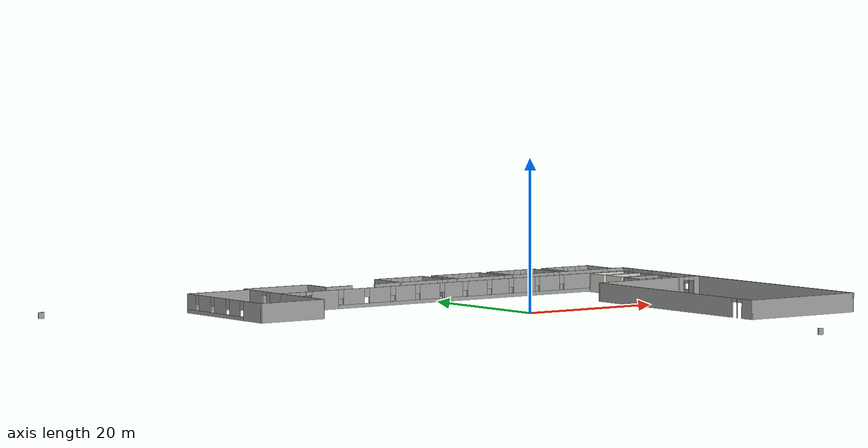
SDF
<?xml version='1.0'?>
<sdf version='1.6'>
  <model name='firstFloor'>
    <pose frame=''>-0.116512 3.07366 0 0 -0 0</pose>
    <link name='Wall_0'>
      <pose frame=''>17.6408 -10.9848 0 0 0 -1.5708</pose>
      <visual name='Wall_0_Visual_0'>
        <pose frame=''>-1.92288 0 1.25 0 -0 0</pose>
        <geometry>
          <box>
            <size>27.1542 0.15 2.5</size>
          </box>
        </geometry>
        <material>
          <script>
            <uri>file://media/materials/scripts/gazebo.material</uri>
            <name>Gazebo/Grey</name>
          </script>
          <ambient>1 1 1 1</ambient>
        </material>
        <meta>
          <layer>0</layer>
        </meta>
      </visual>
      <collision name='Wall_0_Collision_0'>
        <geometry>
          <box>
            <size>27.1542 0.15 2.5</size>
          </box>
        </geometry>
        <pose frame=''>-1.92288 0 1.25 0 -0 0</pose>
      </collision>
      <visual name='Wall_0_Visual_1'>
        <pose frame=''>12.5857 0 1.25 0 -0 0</pose>
        <geometry>
          <box>
            <size>0.062944 0.15 2.5</size>
          </box>
        </geometry>
        <material>
          <script>
            <uri>file://media/materials/scripts/gazebo.material</uri>
            <name>Gazebo/Grey</name>
          </script>
          <ambient>1 1 1 1</ambient>
        </material>
        <meta>
          <layer>0</layer>
        </meta>
      </visual>
      <collision name='Wall_0_Collision_1'>
        <geometry>
          <box>
            <size>0.062944 0.15 2.5</size>
          </box>
        </geometry>
        <pose frame=''>12.5857 0 1.25 0 -0 0</pose>
      </collision>
      <visual name='Wall_0_Visual_2'>
        <pose frame=''>14.5086 0 1.25 0 -0 0</pose>
        <geometry>
          <box>
            <size>1.98281 0.15 2.5</size>
          </box>
        </geometry>
        <material>
          <script>
            <uri>file://media/materials/scripts/gazebo.material</uri>
            <name>Gazebo/Grey</name>
          </script>
          <ambient>1 1 1 1</ambient>
        </material>
        <meta>
          <layer>0</layer>
        </meta>
      </visual>
      <collision name='Wall_0_Collision_2'>
        <geometry>
          <box>
            <size>1.98281 0.15 2.5</size>
          </box>
        </geometry>
        <pose frame=''>14.5086 0 1.25 0 -0 0</pose>
      </collision>
      <visual name='Wall_0_Visual_3'>
        <pose frame=''>12.1042 0 2.25 0 -0 0</pose>
        <geometry>
          <box>
            <size>0.9 0.15 0.5</size>
          </box>
        </geometry>
        <material>
          <script>
            <uri>file://media/materials/scripts/gazebo.material</uri>
            <name>Gazebo/Grey</name>
          </script>
          <ambient>1 1 1 1</ambient>
        </material>
        <meta>
          <layer>0</layer>
        </meta>
      </visual>
      <collision name='Wall_0_Collision_3'>
        <geometry>
          <box>
            <size>0.9 0.15 0.5</size>
          </box>
        </geometry>
        <pose frame=''>12.1042 0 2.25 0 -0 0</pose>
      </collision>
      <visual name='Wall_0_Visual_4'>
        <pose frame=''>13.0672 0 2.25 0 -0 0</pose>
        <geometry>
          <box>
            <size>0.9 0.15 0.5</size>
          </box>
        </geometry>
        <material>
          <script>
            <uri>file://media/materials/scripts/gazebo.material</uri>
            <name>Gazebo/Grey</name>
          </script>
          <ambient>1 1 1 1</ambient>
        </material>
        <meta>
          <layer>0</layer>
        </meta>
      </visual>
      <collision name='Wall_0_Collision_4'>
        <geometry>
          <box>
            <size>0.9 0.15 0.5</size>
          </box>
        </geometry>
        <pose frame=''>13.0672 0 2.25 0 -0 0</pose>
      </collision>
    </link>
    <link name='Wall_1'>
      <collision name='Wall_1_Collision'>
        <geometry>
          <box>
            <size>17.25 0.15 2.5</size>
          </box>
        </geometry>
        <pose frame=''>0 0 1.25 0 -0 0</pose>
      </collision>
      <visual name='Wall_1_Visual'>
        <pose frame=''>0 0 1.25 0 -0 0</pose>
        <geometry>
          <box>
            <size>17.25 0.15 2.5</size>
          </box>
        </geometry>
        <material>
          <script>
            <uri>file://media/materials/scripts/gazebo.material</uri>
            <name>Gazebo/Grey</name>
          </script>
          <ambient>1 1 1 1</ambient>
        </material>
        <meta>
          <layer>0</layer>
        </meta>
      </visual>
      <pose frame=''>26.1908 -26.4098 0 0 -0 0</pose>
    </link>
    <link name='Wall_15'>
      <pose frame=''>2.99839 16.757 0 0 -0 0</pose>
      <visual name='Wall_15_Visual_0'>
        <pose frame=''>-26.7456 0 1.25 0 -0 0</pose>
        <geometry>
          <box>
            <size>3.00874 0.15 2.5</size>
          </box>
        </geometry>
        <material>
          <script>
            <uri>file://media/materials/scripts/gazebo.material</uri>
            <name>Gazebo/Grey</name>
          </script>
          <ambient>1 1 1 1</ambient>
        </material>
        <meta>
          <layer>0</layer>
        </meta>
      </visual>
      <collision name='Wall_15_Collision_0'>
        <geometry>
          <box>
            <size>3.00874 0.15 2.5</size>
          </box>
        </geometry>
        <pose frame=''>-26.7456 0 1.25 0 -0 0</pose>
      </collision>
      <visual name='Wall_15_Visual_1'>
        <pose frame=''>-24.2997 0 1.25 0 -0 0</pose>
        <geometry>
          <box>
            <size>0.083156 0.15 2.5</size>
          </box>
        </geometry>
        <material>
          <script>
            <uri>file://media/materials/scripts/gazebo.material</uri>
            <name>Gazebo/Grey</name>
          </script>
          <ambient>1 1 1 1</ambient>
        </material>
        <meta>
          <layer>0</layer>
        </meta>
      </visual>
      <collision name='Wall_15_Collision_1'>
        <geometry>
          <box>
            <size>0.083156 0.15 2.5</size>
          </box>
        </geometry>
        <pose frame=''>-24.2997 0 1.25 0 -0 0</pose>
      </collision>
      <visual name='Wall_15_Visual_2'>
        <pose frame=''>-21.2466 0 1.25 0 -0 0</pose>
        <geometry>
          <box>
            <size>4.22309 0.15 2.5</size>
          </box>
        </geometry>
        <material>
          <script>
            <uri>file://media/materials/scripts/gazebo.material</uri>
            <name>Gazebo/Grey</name>
          </script>
          <ambient>1 1 1 1</ambient>
        </material>
        <meta>
          <layer>0</layer>
        </meta>
      </visual>
      <collision name='Wall_15_Collision_2'>
        <geometry>
          <box>
            <size>4.22309 0.15 2.5</size>
          </box>
        </geometry>
        <pose frame=''>-21.2466 0 1.25 0 -0 0</pose>
      </collision>
      <visual name='Wall_15_Visual_3'>
        <pose frame=''>4.55749 0 0.25 0 -0 0</pose>
        <geometry>
          <box>
            <size>47.385 0.15 0.5</size>
          </box>
        </geometry>
        <material>
          <script>
            <uri>file://media/materials/scripts/gazebo.material</uri>
            <name>Gazebo/Grey</name>
          </script>
          <ambient>1 1 1 1</ambient>
        </material>
        <meta>
          <layer>0</layer>
        </meta>
      </visual>
      <collision name='Wall_15_Collision_3'>
        <geometry>
          <box>
            <size>47.385 0.15 0.5</size>
          </box>
        </geometry>
        <pose frame=''>4.55749 0 0.25 0 -0 0</pose>
      </collision>
      <visual name='Wall_15_Visual_4'>
        <pose frame=''>-16.6507 0 1.5 0 -0 0</pose>
        <geometry>
          <box>
            <size>3.36858 0.15 2</size>
          </box>
        </geometry>
        <material>
          <script>
            <uri>file://media/materials/scripts/gazebo.material</uri>
            <name>Gazebo/Grey</name>
          </script>
          <ambient>1 1 1 1</ambient>
        </material>
        <meta>
          <layer>0</layer>
        </meta>
      </visual>
      <collision name='Wall_15_Collision_4'>
        <geometry>
          <box>
            <size>3.36858 0.15 2</size>
          </box>
        </geometry>
        <pose frame=''>-16.6507 0 1.5 0 -0 0</pose>
      </collision>
      <visual name='Wall_15_Visual_5'>
        <pose frame=''>-12.4625 0 1.5 0 -0 0</pose>
        <geometry>
          <box>
            <size>3.40791 0.15 2</size>
          </box>
        </geometry>
        <material>
          <script>
            <uri>file://media/materials/scripts/gazebo.material</uri>
            <name>Gazebo/Grey</name>
          </script>
          <ambient>1 1 1 1</ambient>
        </material>
        <meta>
          <layer>0</layer>
        </meta>
      </visual>
      <collision name='Wall_15_Collision_5'>
        <geometry>
          <box>
            <size>3.40791 0.15 2</size>
          </box>
        </geometry>
        <pose frame=''>-12.4625 0 1.5 0 -0 0</pose>
      </collision>
      <visual name='Wall_15_Visual_6'>
        <pose frame=''>-8.34568 0 1.5 0 -0 0</pose>
        <geometry>
          <box>
            <size>3.2257 0.15 2</size>
          </box>
        </geometry>
        <material>
          <script>
            <uri>file://media/materials/scripts/gazebo.material</uri>
            <name>Gazebo/Grey</name>
          </script>
          <ambient>1 1 1 1</ambient>
        </material>
        <meta>
          <layer>0</layer>
        </meta>
      </visual>
      <collision name='Wall_15_Collision_6'>
        <geometry>
          <box>
            <size>3.2257 0.15 2</size>
          </box>
        </geometry>
        <pose frame=''>-8.34568 0 1.5 0 -0 0</pose>
      </collision>
      <visual name='Wall_15_Visual_7'>
        <pose frame=''>-4.31076 0 1.5 0 -0 0</pose>
        <geometry>
          <box>
            <size>3.24413 0.15 2</size>
          </box>
        </geometry>
        <material>
          <script>
            <uri>file://media/materials/scripts/gazebo.material</uri>
            <name>Gazebo/Grey</name>
          </script>
          <ambient>1 1 1 1</ambient>
        </material>
        <meta>
          <layer>0</layer>
        </meta>
      </visual>
      <collision name='Wall_15_Collision_7'>
        <geometry>
          <box>
            <size>3.24413 0.15 2</size>
          </box>
        </geometry>
        <pose frame=''>-4.31076 0 1.5 0 -0 0</pose>
      </collision>
      <visual name='Wall_15_Visual_8'>
        <pose frame=''>-0.385574 0 1.5 0 -0 0</pose>
        <geometry>
          <box>
            <size>3.00624 0.15 2</size>
          </box>
        </geometry>
        <material>
          <script>
            <uri>file://media/materials/scripts/gazebo.material</uri>
            <name>Gazebo/Grey</name>
          </script>
          <ambient>1 1 1 1</ambient>
        </material>
        <meta>
          <layer>0</layer>
        </meta>
      </visual>
      <collision name='Wall_15_Collision_8'>
        <geometry>
          <box>
            <size>3.00624 0.15 2</size>
          </box>
        </geometry>
        <pose frame=''>-0.385574 0 1.5 0 -0 0</pose>
      </collision>
      <visual name='Wall_15_Visual_9'>
        <pose frame=''>3.53961 0 1.5 0 -0 0</pose>
        <geometry>
          <box>
            <size>3.24413 0.15 2</size>
          </box>
        </geometry>
        <material>
          <script>
            <uri>file://media/materials/scripts/gazebo.material</uri>
            <name>Gazebo/Grey</name>
          </script>
          <ambient>1 1 1 1</ambient>
        </material>
        <meta>
          <layer>0</layer>
        </meta>
      </visual>
      <collision name='Wall_15_Collision_9'>
        <geometry>
          <box>
            <size>3.24413 0.15 2</size>
          </box>
        </geometry>
        <pose frame=''>3.53961 0 1.5 0 -0 0</pose>
      </collision>
      <visual name='Wall_15_Visual_10'>
        <pose frame=''>7.39046 0 1.5 0 -0 0</pose>
        <geometry>
          <box>
            <size>2.85756 0.15 2</size>
          </box>
        </geometry>
        <material>
          <script>
            <uri>file://media/materials/scripts/gazebo.material</uri>
            <name>Gazebo/Grey</name>
          </script>
          <ambient>1 1 1 1</ambient>
        </material>
        <meta>
          <layer>0</layer>
        </meta>
      </visual>
      <collision name='Wall_15_Collision_10'>
        <geometry>
          <box>
            <size>2.85756 0.15 2</size>
          </box>
        </geometry>
        <pose frame=''>7.39046 0 1.5 0 -0 0</pose>
      </collision>
      <visual name='Wall_15_Visual_11'>
        <pose frame=''>11.4197 0 1.5 0 -0 0</pose>
        <geometry>
          <box>
            <size>3.60097 0.15 2</size>
          </box>
        </geometry>
        <material>
          <script>
            <uri>file://media/materials/scripts/gazebo.material</uri>
            <name>Gazebo/Grey</name>
          </script>
          <ambient>1 1 1 1</ambient>
        </material>
        <meta>
          <layer>0</layer>
        </meta>
      </visual>
      <collision name='Wall_15_Collision_11'>
        <geometry>
          <box>
            <size>3.60097 0.15 2</size>
          </box>
        </geometry>
        <pose frame=''>11.4197 0 1.5 0 -0 0</pose>
      </collision>
      <visual name='Wall_15_Visual_12'>
        <pose frame=''>15.7166 0 1.5 0 -0 0</pose>
        <geometry>
          <box>
            <size>3.39282 0.15 2</size>
          </box>
        </geometry>
        <material>
          <script>
            <uri>file://media/materials/scripts/gazebo.material</uri>
            <name>Gazebo/Grey</name>
          </script>
          <ambient>1 1 1 1</ambient>
        </material>
        <meta>
          <layer>0</layer>
        </meta>
      </visual>
      <collision name='Wall_15_Collision_12'>
        <geometry>
          <box>
            <size>3.39282 0.15 2</size>
          </box>
        </geometry>
        <pose frame=''>15.7166 0 1.5 0 -0 0</pose>
      </collision>
      <visual name='Wall_15_Visual_13'>
        <pose frame=''>23.2315 0 1.5 0 -0 0</pose>
        <geometry>
          <box>
            <size>10.037 0.15 2</size>
          </box>
        </geometry>
        <material>
          <script>
            <uri>file://media/materials/scripts/gazebo.material</uri>
            <name>Gazebo/Grey</name>
          </script>
          <ambient>1 1 1 1</ambient>
        </material>
        <meta>
          <layer>0</layer>
        </meta>
      </visual>
      <collision name='Wall_15_Collision_13'>
        <geometry>
          <box>
            <size>10.037 0.15 2</size>
          </box>
        </geometry>
        <pose frame=''>23.2315 0 1.5 0 -0 0</pose>
      </collision>
      <visual name='Wall_15_Visual_14'>
        <pose frame=''>-18.735 0 1.9 0 -0 0</pose>
        <geometry>
          <box>
            <size>0.8 0.15 1.2</size>
          </box>
        </geometry>
        <material>
          <script>
            <uri>file://media/materials/scripts/gazebo.material</uri>
            <name>Gazebo/Grey</name>
          </script>
          <ambient>1 1 1 1</ambient>
        </material>
        <meta>
          <layer>0</layer>
        </meta>
      </visual>
      <collision name='Wall_15_Collision_14'>
        <geometry>
          <box>
            <size>0.8 0.15 1.2</size>
          </box>
        </geometry>
        <pose frame=''>-18.735 0 1.9 0 -0 0</pose>
      </collision>
      <visual name='Wall_15_Visual_15'>
        <pose frame=''>-14.5664 0 1.9 0 -0 0</pose>
        <geometry>
          <box>
            <size>0.8 0.15 1.2</size>
          </box>
        </geometry>
        <material>
          <script>
            <uri>file://media/materials/scripts/gazebo.material</uri>
            <name>Gazebo/Grey</name>
          </script>
          <ambient>1 1 1 1</ambient>
        </material>
        <meta>
          <layer>0</layer>
        </meta>
      </visual>
      <collision name='Wall_15_Collision_15'>
        <geometry>
          <box>
            <size>0.8 0.15 1.2</size>
          </box>
        </geometry>
        <pose frame=''>-14.5664 0 1.9 0 -0 0</pose>
      </collision>
      <visual name='Wall_15_Visual_16'>
        <pose frame=''>-10.3585 0 1.9 0 -0 0</pose>
        <geometry>
          <box>
            <size>0.8 0.15 1.2</size>
          </box>
        </geometry>
        <material>
          <script>
            <uri>file://media/materials/scripts/gazebo.material</uri>
            <name>Gazebo/Grey</name>
          </script>
          <ambient>1 1 1 1</ambient>
        </material>
        <meta>
          <layer>0</layer>
        </meta>
      </visual>
      <collision name='Wall_15_Collision_16'>
        <geometry>
          <box>
            <size>0.8 0.15 1.2</size>
          </box>
        </geometry>
        <pose frame=''>-10.3585 0 1.9 0 -0 0</pose>
      </collision>
      <visual name='Wall_15_Visual_17'>
        <pose frame=''>-6.33283 0 1.9 0 -0 0</pose>
        <geometry>
          <box>
            <size>0.8 0.15 1.2</size>
          </box>
        </geometry>
        <material>
          <script>
            <uri>file://media/materials/scripts/gazebo.material</uri>
            <name>Gazebo/Grey</name>
          </script>
          <ambient>1 1 1 1</ambient>
        </material>
        <meta>
          <layer>0</layer>
        </meta>
      </visual>
      <collision name='Wall_15_Collision_17'>
        <geometry>
          <box>
            <size>0.8 0.15 1.2</size>
          </box>
        </geometry>
        <pose frame=''>-6.33283 0 1.9 0 -0 0</pose>
      </collision>
      <visual name='Wall_15_Visual_18'>
        <pose frame=''>-2.2887 0 1.9 0 -0 0</pose>
        <geometry>
          <box>
            <size>0.8 0.15 1.2</size>
          </box>
        </geometry>
        <material>
          <script>
            <uri>file://media/materials/scripts/gazebo.material</uri>
            <name>Gazebo/Grey</name>
          </script>
          <ambient>1 1 1 1</ambient>
        </material>
        <meta>
          <layer>0</layer>
        </meta>
      </visual>
      <collision name='Wall_15_Collision_18'>
        <geometry>
          <box>
            <size>0.8 0.15 1.2</size>
          </box>
        </geometry>
        <pose frame=''>-2.2887 0 1.9 0 -0 0</pose>
      </collision>
      <visual name='Wall_15_Visual_19'>
        <pose frame=''>1.51755 0 1.9 0 -0 0</pose>
        <geometry>
          <box>
            <size>0.8 0.15 1.2</size>
          </box>
        </geometry>
        <material>
          <script>
            <uri>file://media/materials/scripts/gazebo.material</uri>
            <name>Gazebo/Grey</name>
          </script>
          <ambient>1 1 1 1</ambient>
        </material>
        <meta>
          <layer>0</layer>
        </meta>
      </visual>
      <collision name='Wall_15_Collision_19'>
        <geometry>
          <box>
            <size>0.8 0.15 1.2</size>
          </box>
        </geometry>
        <pose frame=''>1.51755 0 1.9 0 -0 0</pose>
      </collision>
      <visual name='Wall_15_Visual_20'>
        <pose frame=''>5.56168 0 1.9 0 -0 0</pose>
        <geometry>
          <box>
            <size>0.8 0.15 1.2</size>
          </box>
        </geometry>
        <material>
          <script>
            <uri>file://media/materials/scripts/gazebo.material</uri>
            <name>Gazebo/Grey</name>
          </script>
          <ambient>1 1 1 1</ambient>
        </material>
        <meta>
          <layer>0</layer>
        </meta>
      </visual>
      <collision name='Wall_15_Collision_20'>
        <geometry>
          <box>
            <size>0.8 0.15 1.2</size>
          </box>
        </geometry>
        <pose frame=''>5.56168 0 1.9 0 -0 0</pose>
      </collision>
      <visual name='Wall_15_Visual_21'>
        <pose frame=''>9.21925 0 1.9 0 -0 0</pose>
        <geometry>
          <box>
            <size>0.8 0.15 1.2</size>
          </box>
        </geometry>
        <material>
          <script>
            <uri>file://media/materials/scripts/gazebo.material</uri>
            <name>Gazebo/Grey</name>
          </script>
          <ambient>1 1 1 1</ambient>
        </material>
        <meta>
          <layer>0</layer>
        </meta>
      </visual>
      <collision name='Wall_15_Collision_21'>
        <geometry>
          <box>
            <size>0.8 0.15 1.2</size>
          </box>
        </geometry>
        <pose frame=''>9.21925 0 1.9 0 -0 0</pose>
      </collision>
      <visual name='Wall_15_Visual_22'>
        <pose frame=''>13.6202 0 1.9 0 -0 0</pose>
        <geometry>
          <box>
            <size>0.8 0.15 1.2</size>
          </box>
        </geometry>
        <material>
          <script>
            <uri>file://media/materials/scripts/gazebo.material</uri>
            <name>Gazebo/Grey</name>
          </script>
          <ambient>1 1 1 1</ambient>
        </material>
        <meta>
          <layer>0</layer>
        </meta>
      </visual>
      <collision name='Wall_15_Collision_22'>
        <geometry>
          <box>
            <size>0.8 0.15 1.2</size>
          </box>
        </geometry>
        <pose frame=''>13.6202 0 1.9 0 -0 0</pose>
      </collision>
      <visual name='Wall_15_Visual_23'>
        <pose frame=''>17.813 0 1.9 0 -0 0</pose>
        <geometry>
          <box>
            <size>0.8 0.15 1.2</size>
          </box>
        </geometry>
        <material>
          <script>
            <uri>file://media/materials/scripts/gazebo.material</uri>
            <name>Gazebo/Grey</name>
          </script>
          <ambient>1 1 1 1</ambient>
        </material>
        <meta>
          <layer>0</layer>
        </meta>
      </visual>
      <collision name='Wall_15_Collision_23'>
        <geometry>
          <box>
            <size>0.8 0.15 1.2</size>
          </box>
        </geometry>
        <pose frame=''>17.813 0 1.9 0 -0 0</pose>
      </collision>
      <visual name='Wall_15_Visual_24'>
        <pose frame=''>-24.7913 0 2.25 0 -0 0</pose>
        <geometry>
          <box>
            <size>0.9 0.15 0.5</size>
          </box>
        </geometry>
        <material>
          <script>
            <uri>file://media/materials/scripts/gazebo.material</uri>
            <name>Gazebo/Grey</name>
          </script>
          <ambient>1 1 1 1</ambient>
        </material>
        <meta>
          <layer>0</layer>
        </meta>
      </visual>
      <collision name='Wall_15_Collision_24'>
        <geometry>
          <box>
            <size>0.9 0.15 0.5</size>
          </box>
        </geometry>
        <pose frame=''>-24.7913 0 2.25 0 -0 0</pose>
      </collision>
      <visual name='Wall_15_Visual_25'>
        <pose frame=''>-23.8081 0 2.25 0 -0 0</pose>
        <geometry>
          <box>
            <size>0.9 0.15 0.5</size>
          </box>
        </geometry>
        <material>
          <script>
            <uri>file://media/materials/scripts/gazebo.material</uri>
            <name>Gazebo/Grey</name>
          </script>
          <ambient>1 1 1 1</ambient>
        </material>
        <meta>
          <layer>0</layer>
        </meta>
      </visual>
      <collision name='Wall_15_Collision_25'>
        <geometry>
          <box>
            <size>0.9 0.15 0.5</size>
          </box>
        </geometry>
        <pose frame=''>-23.8081 0 2.25 0 -0 0</pose>
      </collision>
    </link>
    <link name='Wall_16'>
      <pose frame=''>31.1734 10.582 0 0 0 -1.5708</pose>
      <visual name='Wall_16_Visual_0'>
        <pose frame=''>-5.43447 0 1.25 0 -0 0</pose>
        <geometry>
          <box>
            <size>1.63106 0.15 2.5</size>
          </box>
        </geometry>
        <material>
          <script>
            <uri>file://media/materials/scripts/gazebo.material</uri>
            <name>Gazebo/Grey</name>
          </script>
          <ambient>1 1 1 1</ambient>
        </material>
        <meta>
          <layer>0</layer>
        </meta>
      </visual>
      <collision name='Wall_16_Collision_0'>
        <geometry>
          <box>
            <size>1.63106 0.15 2.5</size>
          </box>
        </geometry>
        <pose frame=''>-5.43447 0 1.25 0 -0 0</pose>
      </collision>
      <visual name='Wall_16_Visual_1'>
        <pose frame=''>-2.26346 0 1.25 0 -0 0</pose>
        <geometry>
          <box>
            <size>2.91096 0.15 2.5</size>
          </box>
        </geometry>
        <material>
          <script>
            <uri>file://media/materials/scripts/gazebo.material</uri>
            <name>Gazebo/Grey</name>
          </script>
          <ambient>1 1 1 1</ambient>
        </material>
        <meta>
          <layer>0</layer>
        </meta>
      </visual>
      <collision name='Wall_16_Collision_1'>
        <geometry>
          <box>
            <size>2.91096 0.15 2.5</size>
          </box>
        </geometry>
        <pose frame=''>-2.26346 0 1.25 0 -0 0</pose>
      </collision>
      <visual name='Wall_16_Visual_2'>
        <pose frame=''>1.45677 0 1.25 0 -0 0</pose>
        <geometry>
          <box>
            <size>2.72949 0.15 2.5</size>
          </box>
        </geometry>
        <material>
          <script>
            <uri>file://media/materials/scripts/gazebo.material</uri>
            <name>Gazebo/Grey</name>
          </script>
          <ambient>1 1 1 1</ambient>
        </material>
        <meta>
          <layer>0</layer>
        </meta>
      </visual>
      <collision name='Wall_16_Collision_2'>
        <geometry>
          <box>
            <size>2.72949 0.15 2.5</size>
          </box>
        </geometry>
        <pose frame=''>1.45677 0 1.25 0 -0 0</pose>
      </collision>
      <visual name='Wall_16_Visual_3'>
        <pose frame=''>4.98576 0 1.25 0 -0 0</pose>
        <geometry>
          <box>
            <size>2.52848 0.15 2.5</size>
          </box>
        </geometry>
        <material>
          <script>
            <uri>file://media/materials/scripts/gazebo.material</uri>
            <name>Gazebo/Grey</name>
          </script>
          <ambient>1 1 1 1</ambient>
        </material>
        <meta>
          <layer>0</layer>
        </meta>
      </visual>
      <collision name='Wall_16_Collision_3'>
        <geometry>
          <box>
            <size>2.52848 0.15 2.5</size>
          </box>
        </geometry>
        <pose frame=''>4.98576 0 1.25 0 -0 0</pose>
      </collision>
      <visual name='Wall_16_Visual_4'>
        <pose frame=''>-4.16894 0 2.25 0 -0 0</pose>
        <geometry>
          <box>
            <size>0.9 0.15 0.5</size>
          </box>
        </geometry>
        <material>
          <script>
            <uri>file://media/materials/scripts/gazebo.material</uri>
            <name>Gazebo/Grey</name>
          </script>
          <ambient>1 1 1 1</ambient>
        </material>
        <meta>
          <layer>0</layer>
        </meta>
      </visual>
      <collision name='Wall_16_Collision_4'>
        <geometry>
          <box>
            <size>0.9 0.15 0.5</size>
          </box>
        </geometry>
        <pose frame=''>-4.16894 0 2.25 0 -0 0</pose>
      </collision>
      <visual name='Wall_16_Visual_5'>
        <pose frame=''>-0.357975 0 2.25 0 -0 0</pose>
        <geometry>
          <box>
            <size>0.9 0.15 0.5</size>
          </box>
        </geometry>
        <material>
          <script>
            <uri>file://media/materials/scripts/gazebo.material</uri>
            <name>Gazebo/Grey</name>
          </script>
          <ambient>1 1 1 1</ambient>
        </material>
        <meta>
          <layer>0</layer>
        </meta>
      </visual>
      <collision name='Wall_16_Collision_5'>
        <geometry>
          <box>
            <size>0.9 0.15 0.5</size>
          </box>
        </geometry>
        <pose frame=''>-0.357975 0 2.25 0 -0 0</pose>
      </collision>
      <visual name='Wall_16_Visual_6'>
        <pose frame=''>3.27151 0 2.25 0 -0 0</pose>
        <geometry>
          <box>
            <size>0.9 0.15 0.5</size>
          </box>
        </geometry>
        <material>
          <script>
            <uri>file://media/materials/scripts/gazebo.material</uri>
            <name>Gazebo/Grey</name>
          </script>
          <ambient>1 1 1 1</ambient>
        </material>
        <meta>
          <layer>0</layer>
        </meta>
      </visual>
      <collision name='Wall_16_Collision_6'>
        <geometry>
          <box>
            <size>0.9 0.15 0.5</size>
          </box>
        </geometry>
        <pose frame=''>3.27151 0 2.25 0 -0 0</pose>
      </collision>
    </link>
    <link name='Wall_2'>
      <collision name='Wall_2_Collision'>
        <geometry>
          <box>
            <size>30.75 0.15 2.5</size>
          </box>
        </geometry>
        <pose frame=''>0 0 1.25 0 -0 0</pose>
      </collision>
      <visual name='Wall_2_Visual'>
        <pose frame=''>0 0 1.25 0 -0 0</pose>
        <geometry>
          <box>
            <size>30.75 0.15 2.5</size>
          </box>
        </geometry>
        <material>
          <script>
            <uri>file://media/materials/scripts/gazebo.material</uri>
            <name>Gazebo/Grey</name>
          </script>
          <ambient>1 1 1 1</ambient>
        </material>
        <meta>
          <layer>0</layer>
        </meta>
      </visual>
      <pose frame=''>34.7408 -11.1098 0 0 -0 1.5708</pose>
    </link>
    <link name='Wall_20'>
      <collision name='Wall_20_Collision'>
        <geometry>
          <box>
            <size>6 0.15 2.5</size>
          </box>
        </geometry>
        <pose frame=''>0 0 1.25 0 -0 0</pose>
      </collision>
      <visual name='Wall_20_Visual'>
        <pose frame=''>0 0 1.25 0 -0 0</pose>
        <geometry>
          <box>
            <size>6 0.15 2.5</size>
          </box>
        </geometry>
        <material>
          <script>
            <uri>file://media/materials/scripts/gazebo.material</uri>
            <name>Gazebo/CeilingTiled</name>
          </script>
          <ambient>1 1 1 1</ambient>
        </material>
        <meta>
          <layer>0</layer>
        </meta>
      </visual>
      <pose frame=''>28.2901 16.1378 0 0 -0 3.14159</pose>
    </link>
    <link name='Wall_21'>
      <collision name='Wall_21_Collision'>
        <geometry>
          <box>
            <size>3 0.15 2.5</size>
          </box>
        </geometry>
        <pose frame=''>0 0 1.25 0 -0 0</pose>
      </collision>
      <visual name='Wall_21_Visual'>
        <pose frame=''>0 0 1.25 0 -0 0</pose>
        <geometry>
          <box>
            <size>3 0.15 2.5</size>
          </box>
        </geometry>
        <material>
          <script>
            <uri>file://media/materials/scripts/gazebo.material</uri>
            <name>Gazebo/CeilingTiled</name>
          </script>
          <ambient>1 1 1 1</ambient>
        </material>
        <meta>
          <layer>0</layer>
        </meta>
      </visual>
      <pose frame=''>25.3651 14.7128 0 0 0 -1.5708</pose>
    </link>
    <link name='Wall_22'>
      <collision name='Wall_22_Collision'>
        <geometry>
          <box>
            <size>6 0.15 2.5</size>
          </box>
        </geometry>
        <pose frame=''>0 0 1.25 0 -0 0</pose>
      </collision>
      <visual name='Wall_22_Visual'>
        <pose frame=''>0 0 1.25 0 -0 0</pose>
        <geometry>
          <box>
            <size>6 0.15 2.5</size>
          </box>
        </geometry>
        <material>
          <script>
            <uri>file://media/materials/scripts/gazebo.material</uri>
            <name>Gazebo/CeilingTiled</name>
          </script>
          <ambient>1 1 1 1</ambient>
        </material>
        <meta>
          <layer>0</layer>
        </meta>
      </visual>
      <pose frame=''>28.2901 13.2878 0 0 -0 0</pose>
    </link>
    <link name='Wall_24'>
      <collision name='Wall_24_Collision'>
        <geometry>
          <box>
            <size>6 0.15 2.5</size>
          </box>
        </geometry>
        <pose frame=''>0 0 1.25 0 -0 0</pose>
      </collision>
      <visual name='Wall_24_Visual'>
        <pose frame=''>0 0 1.25 0 -0 0</pose>
        <geometry>
          <box>
            <size>6 0.15 2.5</size>
          </box>
        </geometry>
        <material>
          <script>
            <uri>file://media/materials/scripts/gazebo.material</uri>
            <name>Gazebo/CeilingTiled</name>
          </script>
          <ambient>1 1 1 1</ambient>
        </material>
        <meta>
          <layer>0</layer>
        </meta>
      </visual>
      <pose frame=''>28.3012 12.5835 0 0 -0 3.14159</pose>
    </link>
    <link name='Wall_25'>
      <collision name='Wall_25_Collision'>
        <geometry>
          <box>
            <size>3.25 0.15 2.5</size>
          </box>
        </geometry>
        <pose frame=''>0 0 1.25 0 -0 0</pose>
      </collision>
      <visual name='Wall_25_Visual'>
        <pose frame=''>0 0 1.25 0 -0 0</pose>
        <geometry>
          <box>
            <size>3.25 0.15 2.5</size>
          </box>
        </geometry>
        <material>
          <script>
            <uri>file://media/materials/scripts/gazebo.material</uri>
            <name>Gazebo/CeilingTiled</name>
          </script>
          <ambient>1 1 1 1</ambient>
        </material>
        <meta>
          <layer>0</layer>
        </meta>
      </visual>
      <pose frame=''>25.3762 11.0335 0 0 0 -1.5708</pose>
    </link>
    <link name='Wall_26'>
      <collision name='Wall_26_Collision'>
        <geometry>
          <box>
            <size>5.75 0.15 2.5</size>
          </box>
        </geometry>
        <pose frame=''>0 0 1.25 0 -0 0</pose>
      </collision>
      <visual name='Wall_26_Visual'>
        <pose frame=''>0 0 1.25 0 -0 0</pose>
        <geometry>
          <box>
            <size>5.75 0.15 2.5</size>
          </box>
        </geometry>
        <material>
          <script>
            <uri>file://media/materials/scripts/gazebo.material</uri>
            <name>Gazebo/CeilingTiled</name>
          </script>
          <ambient>1 1 1 1</ambient>
        </material>
        <meta>
          <layer>0</layer>
        </meta>
      </visual>
      <pose frame=''>28.1762 9.48348 0 0 -0 0</pose>
    </link>
    <link name='Wall_28'>
      <collision name='Wall_28_Collision'>
        <geometry>
          <box>
            <size>6 0.15 2.5</size>
          </box>
        </geometry>
        <pose frame=''>0 0 1.25 0 -0 0</pose>
      </collision>
      <visual name='Wall_28_Visual'>
        <pose frame=''>0 0 1.25 0 -0 0</pose>
        <geometry>
          <box>
            <size>6 0.15 2.5</size>
          </box>
        </geometry>
        <material>
          <script>
            <uri>file://media/materials/scripts/gazebo.material</uri>
            <name>Gazebo/Grey</name>
          </script>
          <ambient>1 1 1 1</ambient>
        </material>
        <meta>
          <layer>0</layer>
        </meta>
      </visual>
      <pose frame=''>28.2321 8.78663 0 0 -0 3.14159</pose>
    </link>
    <link name='Wall_29'>
      <pose frame=''>25.3071 7.23663 0 0 0 -1.5708</pose>
      <visual name='Wall_29_Visual_0'>
        <pose frame=''>-1.14911 0 1.25 0 -0 0</pose>
        <geometry>
          <box>
            <size>0.951772 0.15 2.5</size>
          </box>
        </geometry>
        <material>
          <script>
            <uri>file://media/materials/scripts/gazebo.material</uri>
            <name>Gazebo/Grey</name>
          </script>
          <ambient>1 1 1 1</ambient>
        </material>
        <meta>
          <layer>0</layer>
        </meta>
      </visual>
      <collision name='Wall_29_Collision_0'>
        <geometry>
          <box>
            <size>0.951772 0.15 2.5</size>
          </box>
        </geometry>
        <pose frame=''>-1.14911 0 1.25 0 -0 0</pose>
      </collision>
      <visual name='Wall_29_Visual_1'>
        <pose frame=''>0.475886 0 0.25 0 -0 0</pose>
        <geometry>
          <box>
            <size>2.29823 0.15 0.5</size>
          </box>
        </geometry>
        <material>
          <script>
            <uri>file://media/materials/scripts/gazebo.material</uri>
            <name>Gazebo/Grey</name>
          </script>
          <ambient>1 1 1 1</ambient>
        </material>
        <meta>
          <layer>0</layer>
        </meta>
      </visual>
      <collision name='Wall_29_Collision_1'>
        <geometry>
          <box>
            <size>2.29823 0.15 0.5</size>
          </box>
        </geometry>
        <pose frame=''>0.475886 0 0.25 0 -0 0</pose>
      </collision>
      <visual name='Wall_29_Visual_2'>
        <pose frame=''>0.875886 0 1.5 0 -0 0</pose>
        <geometry>
          <box>
            <size>1.49823 0.15 2</size>
          </box>
        </geometry>
        <material>
          <script>
            <uri>file://media/materials/scripts/gazebo.material</uri>
            <name>Gazebo/Grey</name>
          </script>
          <ambient>1 1 1 1</ambient>
        </material>
        <meta>
          <layer>0</layer>
        </meta>
      </visual>
      <collision name='Wall_29_Collision_2'>
        <geometry>
          <box>
            <size>1.49823 0.15 2</size>
          </box>
        </geometry>
        <pose frame=''>0.875886 0 1.5 0 -0 0</pose>
      </collision>
      <visual name='Wall_29_Visual_3'>
        <pose frame=''>-0.273228 0 1.9 0 -0 0</pose>
        <geometry>
          <box>
            <size>0.8 0.15 1.2</size>
          </box>
        </geometry>
        <material>
          <script>
            <uri>file://media/materials/scripts/gazebo.material</uri>
            <name>Gazebo/Grey</name>
          </script>
          <ambient>1 1 1 1</ambient>
        </material>
        <meta>
          <layer>0</layer>
        </meta>
      </visual>
      <collision name='Wall_29_Collision_3'>
        <geometry>
          <box>
            <size>0.8 0.15 1.2</size>
          </box>
        </geometry>
        <pose frame=''>-0.273228 0 1.9 0 -0 0</pose>
      </collision>
    </link>
    <link name='Wall_30'>
      <collision name='Wall_30_Collision'>
        <geometry>
          <box>
            <size>6 0.15 2.5</size>
          </box>
        </geometry>
        <pose frame=''>0 0 1.25 0 -0 0</pose>
      </collision>
      <visual name='Wall_30_Visual'>
        <pose frame=''>0 0 1.25 0 -0 0</pose>
        <geometry>
          <box>
            <size>6 0.15 2.5</size>
          </box>
        </geometry>
        <material>
          <script>
            <uri>file://media/materials/scripts/gazebo.material</uri>
            <name>Gazebo/Grey</name>
          </script>
          <ambient>1 1 1 1</ambient>
        </material>
        <meta>
          <layer>0</layer>
        </meta>
      </visual>
      <pose frame=''>28.2321 5.68663 0 0 -0 0</pose>
    </link>
    <link name='Wall_32'>
      <pose frame=''>15.7968 20.7947 0 0 -0 3.14159</pose>
      <visual name='Wall_32_Visual_0'>
        <pose frame=''>-17.6843 0 1.25 0 -0 0</pose>
        <geometry>
          <box>
            <size>2.88139 0.15 2.5</size>
          </box>
        </geometry>
        <material>
          <script>
            <uri>file://media/materials/scripts/gazebo.material</uri>
            <name>Gazebo/Grey</name>
          </script>
          <ambient>1 1 1 1</ambient>
        </material>
        <meta>
          <layer>0</layer>
        </meta>
      </visual>
      <collision name='Wall_32_Collision_0'>
        <geometry>
          <box>
            <size>2.88139 0.15 2.5</size>
          </box>
        </geometry>
        <pose frame=''>-17.6843 0 1.25 0 -0 0</pose>
      </collision>
      <visual name='Wall_32_Visual_1'>
        <pose frame=''>-11.0804 0 1.25 0 -0 0</pose>
        <geometry>
          <box>
            <size>8.52647 0.15 2.5</size>
          </box>
        </geometry>
        <material>
          <script>
            <uri>file://media/materials/scripts/gazebo.material</uri>
            <name>Gazebo/Grey</name>
          </script>
          <ambient>1 1 1 1</ambient>
        </material>
        <meta>
          <layer>0</layer>
        </meta>
      </visual>
      <collision name='Wall_32_Collision_1'>
        <geometry>
          <box>
            <size>8.52647 0.15 2.5</size>
          </box>
        </geometry>
        <pose frame=''>-11.0804 0 1.25 0 -0 0</pose>
      </collision>
      <visual name='Wall_32_Visual_2'>
        <pose frame=''>-1.63402 0 1.25 0 -0 0</pose>
        <geometry>
          <box>
            <size>8.56625 0.15 2.5</size>
          </box>
        </geometry>
        <material>
          <script>
            <uri>file://media/materials/scripts/gazebo.material</uri>
            <name>Gazebo/Grey</name>
          </script>
          <ambient>1 1 1 1</ambient>
        </material>
        <meta>
          <layer>0</layer>
        </meta>
      </visual>
      <collision name='Wall_32_Collision_2'>
        <geometry>
          <box>
            <size>8.56625 0.15 2.5</size>
          </box>
        </geometry>
        <pose frame=''>-1.63402 0 1.25 0 -0 0</pose>
      </collision>
      <visual name='Wall_32_Visual_3'>
        <pose frame=''>7.79245 0 1.25 0 -0 0</pose>
        <geometry>
          <box>
            <size>8.4867 0.15 2.5</size>
          </box>
        </geometry>
        <material>
          <script>
            <uri>file://media/materials/scripts/gazebo.material</uri>
            <name>Gazebo/Grey</name>
          </script>
          <ambient>1 1 1 1</ambient>
        </material>
        <meta>
          <layer>0</layer>
        </meta>
      </visual>
      <collision name='Wall_32_Collision_3'>
        <geometry>
          <box>
            <size>8.4867 0.15 2.5</size>
          </box>
        </geometry>
        <pose frame=''>7.79245 0 1.25 0 -0 0</pose>
      </collision>
      <visual name='Wall_32_Visual_4'>
        <pose frame=''>16.0304 0 1.25 0 -0 0</pose>
        <geometry>
          <box>
            <size>6.1892 0.15 2.5</size>
          </box>
        </geometry>
        <material>
          <script>
            <uri>file://media/materials/scripts/gazebo.material</uri>
            <name>Gazebo/Grey</name>
          </script>
          <ambient>1 1 1 1</ambient>
        </material>
        <meta>
          <layer>0</layer>
        </meta>
      </visual>
      <collision name='Wall_32_Collision_4'>
        <geometry>
          <box>
            <size>6.1892 0.15 2.5</size>
          </box>
        </geometry>
        <pose frame=''>16.0304 0 1.25 0 -0 0</pose>
      </collision>
      <visual name='Wall_32_Visual_5'>
        <pose frame=''>-15.7936 0 2.25 0 -0 0</pose>
        <geometry>
          <box>
            <size>0.9 0.15 0.5</size>
          </box>
        </geometry>
        <material>
          <script>
            <uri>file://media/materials/scripts/gazebo.material</uri>
            <name>Gazebo/Grey</name>
          </script>
          <ambient>1 1 1 1</ambient>
        </material>
        <meta>
          <layer>0</layer>
        </meta>
      </visual>
      <collision name='Wall_32_Collision_5'>
        <geometry>
          <box>
            <size>0.9 0.15 0.5</size>
          </box>
        </geometry>
        <pose frame=''>-15.7936 0 2.25 0 -0 0</pose>
      </collision>
      <visual name='Wall_32_Visual_6'>
        <pose frame=''>-6.36714 0 2.25 0 -0 0</pose>
        <geometry>
          <box>
            <size>0.9 0.15 0.5</size>
          </box>
        </geometry>
        <material>
          <script>
            <uri>file://media/materials/scripts/gazebo.material</uri>
            <name>Gazebo/Grey</name>
          </script>
          <ambient>1 1 1 1</ambient>
        </material>
        <meta>
          <layer>0</layer>
        </meta>
      </visual>
      <collision name='Wall_32_Collision_6'>
        <geometry>
          <box>
            <size>0.9 0.15 0.5</size>
          </box>
        </geometry>
        <pose frame=''>-6.36714 0 2.25 0 -0 0</pose>
      </collision>
      <visual name='Wall_32_Visual_7'>
        <pose frame=''>3.0991 0 2.25 0 -0 0</pose>
        <geometry>
          <box>
            <size>0.9 0.15 0.5</size>
          </box>
        </geometry>
        <material>
          <script>
            <uri>file://media/materials/scripts/gazebo.material</uri>
            <name>Gazebo/Grey</name>
          </script>
          <ambient>1 1 1 1</ambient>
        </material>
        <meta>
          <layer>0</layer>
        </meta>
      </visual>
      <collision name='Wall_32_Collision_7'>
        <geometry>
          <box>
            <size>0.9 0.15 0.5</size>
          </box>
        </geometry>
        <pose frame=''>3.0991 0 2.25 0 -0 0</pose>
      </collision>
      <visual name='Wall_32_Visual_8'>
        <pose frame=''>12.4858 0 2.25 0 -0 0</pose>
        <geometry>
          <box>
            <size>0.9 0.15 0.5</size>
          </box>
        </geometry>
        <material>
          <script>
            <uri>file://media/materials/scripts/gazebo.material</uri>
            <name>Gazebo/Grey</name>
          </script>
          <ambient>1 1 1 1</ambient>
        </material>
        <meta>
          <layer>0</layer>
        </meta>
      </visual>
      <collision name='Wall_32_Collision_8'>
        <geometry>
          <box>
            <size>0.9 0.15 0.5</size>
          </box>
        </geometry>
        <pose frame=''>12.4858 0 2.25 0 -0 0</pose>
      </collision>
    </link>
    <link name='Wall_33'>
      <collision name='Wall_33_Collision'>
        <geometry>
          <box>
            <size>5.75 0.15 2.5</size>
          </box>
        </geometry>
        <pose frame=''>0 0 1.25 0 -0 0</pose>
      </collision>
      <visual name='Wall_33_Visual'>
        <pose frame=''>0 0 1.25 0 -0 0</pose>
        <geometry>
          <box>
            <size>5.75 0.15 2.5</size>
          </box>
        </geometry>
        <material>
          <script>
            <uri>file://media/materials/scripts/gazebo.material</uri>
            <name>Gazebo/Grey</name>
          </script>
          <ambient>1 1 1 1</ambient>
        </material>
        <meta>
          <layer>0</layer>
        </meta>
      </visual>
      <pose frame=''>-3.25319 23.5947 0 0 -0 1.5708</pose>
    </link>
    <link name='Wall_34'>
      <pose frame=''>0.671807 26.3947 0 0 -0 0</pose>
      <visual name='Wall_34_Visual_0'>
        <pose frame=''>-3.08954 0 1.25 0 -0 0</pose>
        <geometry>
          <box>
            <size>1.82092 0.15 2.5</size>
          </box>
        </geometry>
        <material>
          <script>
            <uri>file://media/materials/scripts/gazebo.material</uri>
            <name>Gazebo/Grey</name>
          </script>
          <ambient>1 1 1 1</ambient>
        </material>
        <meta>
          <layer>0</layer>
        </meta>
      </visual>
      <collision name='Wall_34_Collision_0'>
        <geometry>
          <box>
            <size>1.82092 0.15 2.5</size>
          </box>
        </geometry>
        <pose frame=''>-3.08954 0 1.25 0 -0 0</pose>
      </collision>
      <visual name='Wall_34_Visual_1'>
        <pose frame=''>0.910461 0 0.25 0 -0 0</pose>
        <geometry>
          <box>
            <size>6.17908 0.15 0.5</size>
          </box>
        </geometry>
        <material>
          <script>
            <uri>file://media/materials/scripts/gazebo.material</uri>
            <name>Gazebo/Grey</name>
          </script>
          <ambient>1 1 1 1</ambient>
        </material>
        <meta>
          <layer>0</layer>
        </meta>
      </visual>
      <collision name='Wall_34_Collision_1'>
        <geometry>
          <box>
            <size>6.17908 0.15 0.5</size>
          </box>
        </geometry>
        <pose frame=''>0.910461 0 0.25 0 -0 0</pose>
      </collision>
      <visual name='Wall_34_Visual_2'>
        <pose frame=''>-0.815585 0 1.5 0 -0 0</pose>
        <geometry>
          <box>
            <size>1.12699 0.15 2</size>
          </box>
        </geometry>
        <material>
          <script>
            <uri>file://media/materials/scripts/gazebo.material</uri>
            <name>Gazebo/Grey</name>
          </script>
          <ambient>1 1 1 1</ambient>
        </material>
        <meta>
          <layer>0</layer>
        </meta>
      </visual>
      <collision name='Wall_34_Collision_2'>
        <geometry>
          <box>
            <size>1.12699 0.15 2</size>
          </box>
        </geometry>
        <pose frame=''>-0.815585 0 1.5 0 -0 0</pose>
      </collision>
      <visual name='Wall_34_Visual_3'>
        <pose frame=''>1.15073 0 1.5 0 -0 0</pose>
        <geometry>
          <box>
            <size>1.20564 0.15 2</size>
          </box>
        </geometry>
        <material>
          <script>
            <uri>file://media/materials/scripts/gazebo.material</uri>
            <name>Gazebo/Grey</name>
          </script>
          <ambient>1 1 1 1</ambient>
        </material>
        <meta>
          <layer>0</layer>
        </meta>
      </visual>
      <collision name='Wall_34_Collision_3'>
        <geometry>
          <box>
            <size>1.20564 0.15 2</size>
          </box>
        </geometry>
        <pose frame=''>1.15073 0 1.5 0 -0 0</pose>
      </collision>
      <visual name='Wall_34_Visual_4'>
        <pose frame=''>3.27677 0 1.5 0 -0 0</pose>
        <geometry>
          <box>
            <size>1.44646 0.15 2</size>
          </box>
        </geometry>
        <material>
          <script>
            <uri>file://media/materials/scripts/gazebo.material</uri>
            <name>Gazebo/Grey</name>
          </script>
          <ambient>1 1 1 1</ambient>
        </material>
        <meta>
          <layer>0</layer>
        </meta>
      </visual>
      <collision name='Wall_34_Collision_4'>
        <geometry>
          <box>
            <size>1.44646 0.15 2</size>
          </box>
        </geometry>
        <pose frame=''>3.27677 0 1.5 0 -0 0</pose>
      </collision>
      <visual name='Wall_34_Visual_5'>
        <pose frame=''>-1.77908 0 1.9 0 -0 0</pose>
        <geometry>
          <box>
            <size>0.8 0.15 1.2</size>
          </box>
        </geometry>
        <material>
          <script>
            <uri>file://media/materials/scripts/gazebo.material</uri>
            <name>Gazebo/Grey</name>
          </script>
          <ambient>1 1 1 1</ambient>
        </material>
        <meta>
          <layer>0</layer>
        </meta>
      </visual>
      <collision name='Wall_34_Collision_5'>
        <geometry>
          <box>
            <size>0.8 0.15 1.2</size>
          </box>
        </geometry>
        <pose frame=''>-1.77908 0 1.9 0 -0 0</pose>
      </collision>
      <visual name='Wall_34_Visual_6'>
        <pose frame=''>0.147907 0 1.9 0 -0 0</pose>
        <geometry>
          <box>
            <size>0.8 0.15 1.2</size>
          </box>
        </geometry>
        <material>
          <script>
            <uri>file://media/materials/scripts/gazebo.material</uri>
            <name>Gazebo/Grey</name>
          </script>
          <ambient>1 1 1 1</ambient>
        </material>
        <meta>
          <layer>0</layer>
        </meta>
      </visual>
      <collision name='Wall_34_Collision_6'>
        <geometry>
          <box>
            <size>0.8 0.15 1.2</size>
          </box>
        </geometry>
        <pose frame=''>0.147907 0 1.9 0 -0 0</pose>
      </collision>
      <visual name='Wall_34_Visual_7'>
        <pose frame=''>2.15354 0 1.9 0 -0 0</pose>
        <geometry>
          <box>
            <size>0.8 0.15 1.2</size>
          </box>
        </geometry>
        <material>
          <script>
            <uri>file://media/materials/scripts/gazebo.material</uri>
            <name>Gazebo/Grey</name>
          </script>
          <ambient>1 1 1 1</ambient>
        </material>
        <meta>
          <layer>0</layer>
        </meta>
      </visual>
      <collision name='Wall_34_Collision_7'>
        <geometry>
          <box>
            <size>0.8 0.15 1.2</size>
          </box>
        </geometry>
        <pose frame=''>2.15354 0 1.9 0 -0 0</pose>
      </collision>
    </link>
    <link name='Wall_35'>
      <collision name='Wall_35_Collision'>
        <geometry>
          <box>
            <size>5.75 0.15 2.5</size>
          </box>
        </geometry>
        <pose frame=''>0 0 1.25 0 -0 0</pose>
      </collision>
      <visual name='Wall_35_Visual'>
        <pose frame=''>0 0 1.25 0 -0 0</pose>
        <geometry>
          <box>
            <size>5.75 0.15 2.5</size>
          </box>
        </geometry>
        <material>
          <script>
            <uri>file://media/materials/scripts/gazebo.material</uri>
            <name>Gazebo/Grey</name>
          </script>
          <ambient>1 1 1 1</ambient>
        </material>
        <meta>
          <layer>0</layer>
        </meta>
      </visual>
      <pose frame=''>4.59681 23.5947 0 0 0 -1.5708</pose>
    </link>
    <link name='Wall_4'>
      <collision name='Wall_4_Collision'>
        <geometry>
          <box>
            <size>31 0.15 2.5</size>
          </box>
        </geometry>
        <pose frame=''>0 0 1.25 0 -0 0</pose>
      </collision>
      <visual name='Wall_4_Visual'>
        <pose frame=''>0 0 1.25 0 -0 0</pose>
        <geometry>
          <box>
            <size>31 0.15 2.5</size>
          </box>
        </geometry>
        <material>
          <script>
            <uri>file://media/materials/scripts/gazebo.material</uri>
            <name>Gazebo/Grey</name>
          </script>
          <ambient>1 1 1 1</ambient>
        </material>
        <meta>
          <layer>0</layer>
        </meta>
      </visual>
      <pose frame=''>34.8468 -10.9803 0 0 0 -1.5708</pose>
    </link>
    <link name='Wall_42'>
      <collision name='Wall_42_Collision'>
        <geometry>
          <box>
            <size>5.75 0.15 2.5</size>
          </box>
        </geometry>
        <pose frame=''>0 0 1.25 0 -0 0</pose>
      </collision>
      <visual name='Wall_42_Visual'>
        <pose frame=''>0 0 1.25 0 -0 0</pose>
        <geometry>
          <box>
            <size>5.75 0.15 2.5</size>
          </box>
        </geometry>
        <material>
          <script>
            <uri>file://media/materials/scripts/gazebo.material</uri>
            <name>Gazebo/Grey</name>
          </script>
          <ambient>1 1 1 1</ambient>
        </material>
        <meta>
          <layer>0</layer>
        </meta>
      </visual>
      <pose frame=''>6.13497 23.5303 0 0 -0 1.5708</pose>
    </link>
    <link name='Wall_43'>
      <pose frame=''>10.1395 26.3303 0 0 -0 0</pose>
      <visual name='Wall_43_Visual_0'>
        <pose frame=''>-3.23474 0 1.25 0 -0 0</pose>
        <geometry>
          <box>
            <size>1.68961 0.15 2.5</size>
          </box>
        </geometry>
        <material>
          <script>
            <uri>file://media/materials/scripts/gazebo.material</uri>
            <name>Gazebo/Grey</name>
          </script>
          <ambient>1 1 1 1</ambient>
        </material>
        <meta>
          <layer>0</layer>
        </meta>
      </visual>
      <collision name='Wall_43_Collision_0'>
        <geometry>
          <box>
            <size>1.68961 0.15 2.5</size>
          </box>
        </geometry>
        <pose frame=''>-3.23474 0 1.25 0 -0 0</pose>
      </collision>
      <visual name='Wall_43_Visual_1'>
        <pose frame=''>0.844804 0 0.25 0 -0 0</pose>
        <geometry>
          <box>
            <size>6.46949 0.15 0.5</size>
          </box>
        </geometry>
        <material>
          <script>
            <uri>file://media/materials/scripts/gazebo.material</uri>
            <name>Gazebo/Grey</name>
          </script>
          <ambient>1 1 1 1</ambient>
        </material>
        <meta>
          <layer>0</layer>
        </meta>
      </visual>
      <collision name='Wall_43_Collision_1'>
        <geometry>
          <box>
            <size>6.46949 0.15 0.5</size>
          </box>
        </geometry>
        <pose frame=''>0.844804 0 0.25 0 -0 0</pose>
      </collision>
      <visual name='Wall_43_Visual_2'>
        <pose frame=''>-0.975766 0 1.5 0 -0 0</pose>
        <geometry>
          <box>
            <size>1.22835 0.15 2</size>
          </box>
        </geometry>
        <material>
          <script>
            <uri>file://media/materials/scripts/gazebo.material</uri>
            <name>Gazebo/Grey</name>
          </script>
          <ambient>1 1 1 1</ambient>
        </material>
        <meta>
          <layer>0</layer>
        </meta>
      </visual>
      <collision name='Wall_43_Collision_2'>
        <geometry>
          <box>
            <size>1.22835 0.15 2</size>
          </box>
        </geometry>
        <pose frame=''>-0.975766 0 1.5 0 -0 0</pose>
      </collision>
      <visual name='Wall_43_Visual_3'>
        <pose frame=''>1.07859 0 1.5 0 -0 0</pose>
        <geometry>
          <box>
            <size>1.28036 0.15 2</size>
          </box>
        </geometry>
        <material>
          <script>
            <uri>file://media/materials/scripts/gazebo.material</uri>
            <name>Gazebo/Grey</name>
          </script>
          <ambient>1 1 1 1</ambient>
        </material>
        <meta>
          <layer>0</layer>
        </meta>
      </visual>
      <collision name='Wall_43_Collision_3'>
        <geometry>
          <box>
            <size>1.28036 0.15 2</size>
          </box>
        </geometry>
        <pose frame=''>1.07859 0 1.5 0 -0 0</pose>
      </collision>
      <visual name='Wall_43_Visual_4'>
        <pose frame=''>3.29916 0 1.5 0 -0 0</pose>
        <geometry>
          <box>
            <size>1.56078 0.15 2</size>
          </box>
        </geometry>
        <material>
          <script>
            <uri>file://media/materials/scripts/gazebo.material</uri>
            <name>Gazebo/Grey</name>
          </script>
          <ambient>1 1 1 1</ambient>
        </material>
        <meta>
          <layer>0</layer>
        </meta>
      </visual>
      <collision name='Wall_43_Collision_4'>
        <geometry>
          <box>
            <size>1.56078 0.15 2</size>
          </box>
        </geometry>
        <pose frame=''>3.29916 0 1.5 0 -0 0</pose>
      </collision>
      <visual name='Wall_43_Visual_5'>
        <pose frame=''>-1.98994 0 1.9 0 -0 0</pose>
        <geometry>
          <box>
            <size>0.8 0.15 1.2</size>
          </box>
        </geometry>
        <material>
          <script>
            <uri>file://media/materials/scripts/gazebo.material</uri>
            <name>Gazebo/Grey</name>
          </script>
          <ambient>1 1 1 1</ambient>
        </material>
        <meta>
          <layer>0</layer>
        </meta>
      </visual>
      <collision name='Wall_43_Collision_5'>
        <geometry>
          <box>
            <size>0.8 0.15 1.2</size>
          </box>
        </geometry>
        <pose frame=''>-1.98994 0 1.9 0 -0 0</pose>
      </collision>
      <visual name='Wall_43_Visual_6'>
        <pose frame=''>0.038408 0 1.9 0 -0 0</pose>
        <geometry>
          <box>
            <size>0.8 0.15 1.2</size>
          </box>
        </geometry>
        <material>
          <script>
            <uri>file://media/materials/scripts/gazebo.material</uri>
            <name>Gazebo/Grey</name>
          </script>
          <ambient>1 1 1 1</ambient>
        </material>
        <meta>
          <layer>0</layer>
        </meta>
      </visual>
      <collision name='Wall_43_Collision_6'>
        <geometry>
          <box>
            <size>0.8 0.15 1.2</size>
          </box>
        </geometry>
        <pose frame=''>0.038408 0 1.9 0 -0 0</pose>
      </collision>
      <visual name='Wall_43_Visual_7'>
        <pose frame=''>2.11877 0 1.9 0 -0 0</pose>
        <geometry>
          <box>
            <size>0.8 0.15 1.2</size>
          </box>
        </geometry>
        <material>
          <script>
            <uri>file://media/materials/scripts/gazebo.material</uri>
            <name>Gazebo/Grey</name>
          </script>
          <ambient>1 1 1 1</ambient>
        </material>
        <meta>
          <layer>0</layer>
        </meta>
      </visual>
      <collision name='Wall_43_Collision_7'>
        <geometry>
          <box>
            <size>0.8 0.15 1.2</size>
          </box>
        </geometry>
        <pose frame=''>2.11877 0 1.9 0 -0 0</pose>
      </collision>
    </link>
    <link name='Wall_44'>
      <collision name='Wall_44_Collision'>
        <geometry>
          <box>
            <size>5.75 0.15 2.5</size>
          </box>
        </geometry>
        <pose frame=''>0 0 1.25 0 -0 0</pose>
      </collision>
      <visual name='Wall_44_Visual'>
        <pose frame=''>0 0 1.25 0 -0 0</pose>
        <geometry>
          <box>
            <size>5.75 0.15 2.5</size>
          </box>
        </geometry>
        <material>
          <script>
            <uri>file://media/materials/scripts/gazebo.material</uri>
            <name>Gazebo/Grey</name>
          </script>
          <ambient>1 1 1 1</ambient>
        </material>
        <meta>
          <layer>0</layer>
        </meta>
      </visual>
      <pose frame=''>14.1043 23.5303 0 0 0 -1.5708</pose>
    </link>
    <link name='Wall_46'>
      <collision name='Wall_46_Collision'>
        <geometry>
          <box>
            <size>5.75 0.15 2.5</size>
          </box>
        </geometry>
        <pose frame=''>0 0 1.25 0 -0 0</pose>
      </collision>
      <visual name='Wall_46_Visual'>
        <pose frame=''>0 0 1.25 0 -0 0</pose>
        <geometry>
          <box>
            <size>5.75 0.15 2.5</size>
          </box>
        </geometry>
        <material>
          <script>
            <uri>file://media/materials/scripts/gazebo.material</uri>
            <name>Gazebo/Grey</name>
          </script>
          <ambient>1 1 1 1</ambient>
        </material>
        <meta>
          <layer>0</layer>
        </meta>
      </visual>
      <pose frame=''>15.5217 23.5782 0 0 0 -1.5708</pose>
    </link>
    <link name='Wall_48'>
      <pose frame=''>19.5461 26.3782 0 0 -0 0</pose>
      <visual name='Wall_48_Visual_0'>
        <pose frame=''>-3.24117 0 1.25 0 -0 0</pose>
        <geometry>
          <box>
            <size>1.71653 0.15 2.5</size>
          </box>
        </geometry>
        <material>
          <script>
            <uri>file://media/materials/scripts/gazebo.material</uri>
            <name>Gazebo/Grey</name>
          </script>
          <ambient>1 1 1 1</ambient>
        </material>
        <meta>
          <layer>0</layer>
        </meta>
      </visual>
      <collision name='Wall_48_Collision_0'>
        <geometry>
          <box>
            <size>1.71653 0.15 2.5</size>
          </box>
        </geometry>
        <pose frame=''>-3.24117 0 1.25 0 -0 0</pose>
      </collision>
      <visual name='Wall_48_Visual_1'>
        <pose frame=''>0.858265 0 0.25 0 -0 0</pose>
        <geometry>
          <box>
            <size>6.48234 0.15 0.5</size>
          </box>
        </geometry>
        <material>
          <script>
            <uri>file://media/materials/scripts/gazebo.material</uri>
            <name>Gazebo/Grey</name>
          </script>
          <ambient>1 1 1 1</ambient>
        </material>
        <meta>
          <layer>0</layer>
        </meta>
      </visual>
      <collision name='Wall_48_Collision_1'>
        <geometry>
          <box>
            <size>6.48234 0.15 0.5</size>
          </box>
        </geometry>
        <pose frame=''>0.858265 0 0.25 0 -0 0</pose>
      </collision>
      <visual name='Wall_48_Visual_2'>
        <pose frame=''>-0.96873 0 1.5 0 -0 0</pose>
        <geometry>
          <box>
            <size>1.22835 0.15 2</size>
          </box>
        </geometry>
        <material>
          <script>
            <uri>file://media/materials/scripts/gazebo.material</uri>
            <name>Gazebo/Grey</name>
          </script>
          <ambient>1 1 1 1</ambient>
        </material>
        <meta>
          <layer>0</layer>
        </meta>
      </visual>
      <collision name='Wall_48_Collision_2'>
        <geometry>
          <box>
            <size>1.22835 0.15 2</size>
          </box>
        </geometry>
        <pose frame=''>-0.96873 0 1.5 0 -0 0</pose>
      </collision>
      <visual name='Wall_48_Visual_3'>
        <pose frame=''>1.04974 0 1.5 0 -0 0</pose>
        <geometry>
          <box>
            <size>1.2086 0.15 2</size>
          </box>
        </geometry>
        <material>
          <script>
            <uri>file://media/materials/scripts/gazebo.material</uri>
            <name>Gazebo/Grey</name>
          </script>
          <ambient>1 1 1 1</ambient>
        </material>
        <meta>
          <layer>0</layer>
        </meta>
      </visual>
      <collision name='Wall_48_Collision_3'>
        <geometry>
          <box>
            <size>1.2086 0.15 2</size>
          </box>
        </geometry>
        <pose frame=''>1.04974 0 1.5 0 -0 0</pose>
      </collision>
      <visual name='Wall_48_Visual_4'>
        <pose frame=''>3.27674 0 1.5 0 -0 0</pose>
        <geometry>
          <box>
            <size>1.64539 0.15 2</size>
          </box>
        </geometry>
        <material>
          <script>
            <uri>file://media/materials/scripts/gazebo.material</uri>
            <name>Gazebo/Grey</name>
          </script>
          <ambient>1 1 1 1</ambient>
        </material>
        <meta>
          <layer>0</layer>
        </meta>
      </visual>
      <collision name='Wall_48_Collision_4'>
        <geometry>
          <box>
            <size>1.64539 0.15 2</size>
          </box>
        </geometry>
        <pose frame=''>3.27674 0 1.5 0 -0 0</pose>
      </collision>
      <visual name='Wall_48_Visual_5'>
        <pose frame=''>-1.9829 0 1.9 0 -0 0</pose>
        <geometry>
          <box>
            <size>0.8 0.15 1.2</size>
          </box>
        </geometry>
        <material>
          <script>
            <uri>file://media/materials/scripts/gazebo.material</uri>
            <name>Gazebo/Grey</name>
          </script>
          <ambient>1 1 1 1</ambient>
        </material>
        <meta>
          <layer>0</layer>
        </meta>
      </visual>
      <collision name='Wall_48_Collision_5'>
        <geometry>
          <box>
            <size>0.8 0.15 1.2</size>
          </box>
        </geometry>
        <pose frame=''>-1.9829 0 1.9 0 -0 0</pose>
      </collision>
      <visual name='Wall_48_Visual_6'>
        <pose frame=''>0.045444 0 1.9 0 -0 0</pose>
        <geometry>
          <box>
            <size>0.8 0.15 1.2</size>
          </box>
        </geometry>
        <material>
          <script>
            <uri>file://media/materials/scripts/gazebo.material</uri>
            <name>Gazebo/Grey</name>
          </script>
          <ambient>1 1 1 1</ambient>
        </material>
        <meta>
          <layer>0</layer>
        </meta>
      </visual>
      <collision name='Wall_48_Collision_6'>
        <geometry>
          <box>
            <size>0.8 0.15 1.2</size>
          </box>
        </geometry>
        <pose frame=''>0.045444 0 1.9 0 -0 0</pose>
      </collision>
      <visual name='Wall_48_Visual_7'>
        <pose frame=''>2.05404 0 1.9 0 -0 0</pose>
        <geometry>
          <box>
            <size>0.8 0.15 1.2</size>
          </box>
        </geometry>
        <material>
          <script>
            <uri>file://media/materials/scripts/gazebo.material</uri>
            <name>Gazebo/Grey</name>
          </script>
          <ambient>1 1 1 1</ambient>
        </material>
        <meta>
          <layer>0</layer>
        </meta>
      </visual>
      <collision name='Wall_48_Collision_7'>
        <geometry>
          <box>
            <size>0.8 0.15 1.2</size>
          </box>
        </geometry>
        <pose frame=''>2.05404 0 1.9 0 -0 0</pose>
      </collision>
    </link>
    <link name='Wall_49'>
      <collision name='Wall_49_Collision'>
        <geometry>
          <box>
            <size>5.75 0.15 2.5</size>
          </box>
        </geometry>
        <pose frame=''>0 0 1.25 0 -0 0</pose>
      </collision>
      <visual name='Wall_49_Visual'>
        <pose frame=''>0 0 1.25 0 -0 0</pose>
        <geometry>
          <box>
            <size>5.75 0.15 2.5</size>
          </box>
        </geometry>
        <material>
          <script>
            <uri>file://media/materials/scripts/gazebo.material</uri>
            <name>Gazebo/Grey</name>
          </script>
          <ambient>1 1 1 1</ambient>
        </material>
        <meta>
          <layer>0</layer>
        </meta>
      </visual>
      <pose frame=''>23.5705 23.5384 0 0 0 -1.5708</pose>
    </link>
    <link name='Wall_51'>
      <collision name='Wall_51_Collision'>
        <geometry>
          <box>
            <size>5.75 0.15 2.5</size>
          </box>
        </geometry>
        <pose frame=''>0 0 1.25 0 -0 0</pose>
      </collision>
      <visual name='Wall_51_Visual'>
        <pose frame=''>0 0 1.25 0 -0 0</pose>
        <geometry>
          <box>
            <size>5.75 0.15 2.5</size>
          </box>
        </geometry>
        <material>
          <script>
            <uri>file://media/materials/scripts/gazebo.material</uri>
            <name>Gazebo/Grey</name>
          </script>
          <ambient>1 1 1 1</ambient>
        </material>
        <meta>
          <layer>0</layer>
        </meta>
      </visual>
      <pose frame=''>24.9879 23.6098 0 0 -0 1.5708</pose>
    </link>
    <link name='Wall_53'>
      <pose frame=''>29.0322 26.4098 0 0 -0 0</pose>
      <visual name='Wall_53_Visual_0'>
        <pose frame=''>-3.35683 0 1.25 0 -0 0</pose>
        <geometry>
          <box>
            <size>1.52499 0.15 2.5</size>
          </box>
        </geometry>
        <material>
          <script>
            <uri>file://media/materials/scripts/gazebo.material</uri>
            <name>Gazebo/Grey</name>
          </script>
          <ambient>1 1 1 1</ambient>
        </material>
        <meta>
          <layer>0</layer>
        </meta>
      </visual>
      <collision name='Wall_53_Collision_0'>
        <geometry>
          <box>
            <size>1.52499 0.15 2.5</size>
          </box>
        </geometry>
        <pose frame=''>-3.35683 0 1.25 0 -0 0</pose>
      </collision>
      <visual name='Wall_53_Visual_1'>
        <pose frame=''>0.762497 0 0.25 0 -0 0</pose>
        <geometry>
          <box>
            <size>6.71365 0.15 0.5</size>
          </box>
        </geometry>
        <material>
          <script>
            <uri>file://media/materials/scripts/gazebo.material</uri>
            <name>Gazebo/Grey</name>
          </script>
          <ambient>1 1 1 1</ambient>
        </material>
        <meta>
          <layer>0</layer>
        </meta>
      </visual>
      <collision name='Wall_53_Collision_1'>
        <geometry>
          <box>
            <size>6.71365 0.15 0.5</size>
          </box>
        </geometry>
        <pose frame=''>0.762497 0 0.25 0 -0 0</pose>
      </collision>
      <visual name='Wall_53_Visual_2'>
        <pose frame=''>-1.06856 0 1.5 0 -0 0</pose>
        <geometry>
          <box>
            <size>1.45153 0.15 2</size>
          </box>
        </geometry>
        <material>
          <script>
            <uri>file://media/materials/scripts/gazebo.material</uri>
            <name>Gazebo/Grey</name>
          </script>
          <ambient>1 1 1 1</ambient>
        </material>
        <meta>
          <layer>0</layer>
        </meta>
      </visual>
      <collision name='Wall_53_Collision_2'>
        <geometry>
          <box>
            <size>1.45153 0.15 2</size>
          </box>
        </geometry>
        <pose frame=''>-1.06856 0 1.5 0 -0 0</pose>
      </collision>
      <visual name='Wall_53_Visual_3'>
        <pose frame=''>1.10034 0 1.5 0 -0 0</pose>
        <geometry>
          <box>
            <size>1.28627 0.15 2</size>
          </box>
        </geometry>
        <material>
          <script>
            <uri>file://media/materials/scripts/gazebo.material</uri>
            <name>Gazebo/Grey</name>
          </script>
          <ambient>1 1 1 1</ambient>
        </material>
        <meta>
          <layer>0</layer>
        </meta>
      </visual>
      <collision name='Wall_53_Collision_3'>
        <geometry>
          <box>
            <size>1.28627 0.15 2</size>
          </box>
        </geometry>
        <pose frame=''>1.10034 0 1.5 0 -0 0</pose>
      </collision>
      <visual name='Wall_53_Visual_4'>
        <pose frame=''>3.3314 0 1.5 0 -0 0</pose>
        <geometry>
          <box>
            <size>1.57585 0.15 2</size>
          </box>
        </geometry>
        <material>
          <script>
            <uri>file://media/materials/scripts/gazebo.material</uri>
            <name>Gazebo/Grey</name>
          </script>
          <ambient>1 1 1 1</ambient>
        </material>
        <meta>
          <layer>0</layer>
        </meta>
      </visual>
      <collision name='Wall_53_Collision_4'>
        <geometry>
          <box>
            <size>1.57585 0.15 2</size>
          </box>
        </geometry>
        <pose frame=''>3.3314 0 1.5 0 -0 0</pose>
      </collision>
      <visual name='Wall_53_Visual_5'>
        <pose frame=''>-2.19433 0 1.9 0 -0 0</pose>
        <geometry>
          <box>
            <size>0.8 0.15 1.2</size>
          </box>
        </geometry>
        <material>
          <script>
            <uri>file://media/materials/scripts/gazebo.material</uri>
            <name>Gazebo/Grey</name>
          </script>
          <ambient>1 1 1 1</ambient>
        </material>
        <meta>
          <layer>0</layer>
        </meta>
      </visual>
      <collision name='Wall_53_Collision_5'>
        <geometry>
          <box>
            <size>0.8 0.15 1.2</size>
          </box>
        </geometry>
        <pose frame=''>-2.19433 0 1.9 0 -0 0</pose>
      </collision>
      <visual name='Wall_53_Visual_6'>
        <pose frame=''>0.057199 0 1.9 0 -0 0</pose>
        <geometry>
          <box>
            <size>0.8 0.15 1.2</size>
          </box>
        </geometry>
        <material>
          <script>
            <uri>file://media/materials/scripts/gazebo.material</uri>
            <name>Gazebo/Grey</name>
          </script>
          <ambient>1 1 1 1</ambient>
        </material>
        <meta>
          <layer>0</layer>
        </meta>
      </visual>
      <collision name='Wall_53_Collision_6'>
        <geometry>
          <box>
            <size>0.8 0.15 1.2</size>
          </box>
        </geometry>
        <pose frame=''>0.057199 0 1.9 0 -0 0</pose>
      </collision>
      <visual name='Wall_53_Visual_7'>
        <pose frame=''>2.14347 0 1.9 0 -0 0</pose>
        <geometry>
          <box>
            <size>0.8 0.15 1.2</size>
          </box>
        </geometry>
        <material>
          <script>
            <uri>file://media/materials/scripts/gazebo.material</uri>
            <name>Gazebo/Grey</name>
          </script>
          <ambient>1 1 1 1</ambient>
        </material>
        <meta>
          <layer>0</layer>
        </meta>
      </visual>
      <collision name='Wall_53_Collision_7'>
        <geometry>
          <box>
            <size>0.8 0.15 1.2</size>
          </box>
        </geometry>
        <pose frame=''>2.14347 0 1.9 0 -0 0</pose>
      </collision>
    </link>
    <link name='Wall_54'>
      <collision name='Wall_54_Collision'>
        <geometry>
          <box>
            <size>5.75 0.15 2.5</size>
          </box>
        </geometry>
        <pose frame=''>0 0 1.25 0 -0 0</pose>
      </collision>
      <visual name='Wall_54_Visual'>
        <pose frame=''>0 0 1.25 0 -0 0</pose>
        <geometry>
          <box>
            <size>5.75 0.15 2.5</size>
          </box>
        </geometry>
        <material>
          <script>
            <uri>file://media/materials/scripts/gazebo.material</uri>
            <name>Gazebo/Grey</name>
          </script>
          <ambient>1 1 1 1</ambient>
        </material>
        <meta>
          <layer>0</layer>
        </meta>
      </visual>
      <pose frame=''>33.0368 23.6098 0 0 0 -1.5708</pose>
    </link>
    <link name='Wall_56'>
      <collision name='Wall_56_Collision'>
        <geometry>
          <box>
            <size>10.25 0.15 2.5</size>
          </box>
        </geometry>
        <pose frame=''>0 0 1.25 0 -0 0</pose>
      </collision>
      <visual name='Wall_56_Visual'>
        <pose frame=''>0 0 1.25 0 -0 0</pose>
        <geometry>
          <box>
            <size>10.25 0.15 2.5</size>
          </box>
        </geometry>
        <material>
          <script>
            <uri>file://media/materials/scripts/gazebo.material</uri>
            <name>Gazebo/Grey</name>
          </script>
          <ambient>1 1 1 1</ambient>
        </material>
        <meta>
          <layer>0</layer>
        </meta>
      </visual>
      <pose frame=''>-20.1968 25.1054 0 0 -0 0</pose>
    </link>
    <link name='Wall_57'>
      <collision name='Wall_57_Collision'>
        <geometry>
          <box>
            <size>4.25 0.15 2.5</size>
          </box>
        </geometry>
        <pose frame=''>0 0 1.25 0 -0 0</pose>
      </collision>
      <visual name='Wall_57_Visual'>
        <pose frame=''>0 0 1.25 0 -0 0</pose>
        <geometry>
          <box>
            <size>4.25 0.15 2.5</size>
          </box>
        </geometry>
        <material>
          <script>
            <uri>file://media/materials/scripts/gazebo.material</uri>
            <name>Gazebo/Grey</name>
          </script>
          <ambient>1 1 1 1</ambient>
        </material>
        <meta>
          <layer>0</layer>
        </meta>
      </visual>
      <pose frame=''>-15.1468 23.0554 0 0 0 -1.5708</pose>
    </link>
    <link name='Wall_59'>
      <pose frame=''>-25.2468 16.0554 0 0 0 -1.5708</pose>
      <visual name='Wall_59_Visual_0'>
        <pose frame=''>-6.94813 0 1.25 0 -0 0</pose>
        <geometry>
          <box>
            <size>4.35374 0.15 2.5</size>
          </box>
        </geometry>
        <material>
          <script>
            <uri>file://media/materials/scripts/gazebo.material</uri>
            <name>Gazebo/Grey</name>
          </script>
          <ambient>1 1 1 1</ambient>
        </material>
        <meta>
          <layer>0</layer>
        </meta>
      </visual>
      <collision name='Wall_59_Collision_0'>
        <geometry>
          <box>
            <size>4.35374 0.15 2.5</size>
          </box>
        </geometry>
        <pose frame=''>-6.94813 0 1.25 0 -0 0</pose>
      </collision>
      <visual name='Wall_59_Visual_1'>
        <pose frame=''>2.62687 0 1.25 0 -0 0</pose>
        <geometry>
          <box>
            <size>12.9963 0.15 2.5</size>
          </box>
        </geometry>
        <material>
          <script>
            <uri>file://media/materials/scripts/gazebo.material</uri>
            <name>Gazebo/Grey</name>
          </script>
          <ambient>1 1 1 1</ambient>
        </material>
        <meta>
          <layer>0</layer>
        </meta>
      </visual>
      <collision name='Wall_59_Collision_1'>
        <geometry>
          <box>
            <size>12.9963 0.15 2.5</size>
          </box>
        </geometry>
        <pose frame=''>2.62687 0 1.25 0 -0 0</pose>
      </collision>
      <visual name='Wall_59_Visual_2'>
        <pose frame=''>3.05031 0 1.25 0 -0 0</pose>
        <geometry>
          <box>
            <size>12.1494 0.15 2.5</size>
          </box>
        </geometry>
        <material>
          <script>
            <uri>file://media/materials/scripts/gazebo.material</uri>
            <name>Gazebo/Grey</name>
          </script>
          <ambient>1 1 1 1</ambient>
        </material>
        <meta>
          <layer>0</layer>
        </meta>
      </visual>
      <collision name='Wall_59_Collision_2'>
        <geometry>
          <box>
            <size>12.1494 0.15 2.5</size>
          </box>
        </geometry>
        <pose frame=''>3.05031 0 1.25 0 -0 0</pose>
      </collision>
      <visual name='Wall_59_Visual_3'>
        <pose frame=''>-4.34782 0 2.25 0 -0 0</pose>
        <geometry>
          <box>
            <size>0.846882 0.15 0.5</size>
          </box>
        </geometry>
        <material>
          <script>
            <uri>file://media/materials/scripts/gazebo.material</uri>
            <name>Gazebo/Grey</name>
          </script>
          <ambient>1 1 1 1</ambient>
        </material>
        <meta>
          <layer>0</layer>
        </meta>
      </visual>
      <collision name='Wall_59_Collision_3'>
        <geometry>
          <box>
            <size>0.846882 0.15 0.5</size>
          </box>
        </geometry>
        <pose frame=''>-4.34782 0 2.25 0 -0 0</pose>
      </collision>
    </link>
    <link name='Wall_60'>
      <collision name='Wall_60_Collision'>
        <geometry>
          <box>
            <size>9.75 0.15 2.5</size>
          </box>
        </geometry>
        <pose frame=''>0 0 1.25 0 -0 0</pose>
      </collision>
      <visual name='Wall_60_Visual'>
        <pose frame=''>0 0 1.25 0 -0 0</pose>
        <geometry>
          <box>
            <size>9.75 0.15 2.5</size>
          </box>
        </geometry>
        <material>
          <script>
            <uri>file://media/materials/scripts/gazebo.material</uri>
            <name>Gazebo/Grey</name>
          </script>
          <ambient>1 1 1 1</ambient>
        </material>
        <meta>
          <layer>0</layer>
        </meta>
      </visual>
      <pose frame=''>-30.0468 7.00542 0 0 -0 3.14159</pose>
    </link>
    <link name='Wall_61'>
      <pose frame=''>-34.8468 15.4304 0 0 -0 1.5708</pose>
      <visual name='Wall_61_Visual_0'>
        <pose frame=''>-6.47123 0 1.25 0 -0 0</pose>
        <geometry>
          <box>
            <size>4.05754 0.15 2.5</size>
          </box>
        </geometry>
        <material>
          <script>
            <uri>file://media/materials/scripts/gazebo.material</uri>
            <name>Gazebo/Grey</name>
          </script>
          <ambient>1 1 1 1</ambient>
        </material>
        <meta>
          <layer>0</layer>
        </meta>
      </visual>
      <collision name='Wall_61_Collision_0'>
        <geometry>
          <box>
            <size>4.05754 0.15 2.5</size>
          </box>
        </geometry>
        <pose frame=''>-6.47123 0 1.25 0 -0 0</pose>
      </collision>
      <visual name='Wall_61_Visual_1'>
        <pose frame=''>2.02877 0 0.25 0 -0 0</pose>
        <geometry>
          <box>
            <size>12.9425 0.15 0.5</size>
          </box>
        </geometry>
        <material>
          <script>
            <uri>file://media/materials/scripts/gazebo.material</uri>
            <name>Gazebo/Grey</name>
          </script>
          <ambient>1 1 1 1</ambient>
        </material>
        <meta>
          <layer>0</layer>
        </meta>
      </visual>
      <collision name='Wall_61_Collision_1'>
        <geometry>
          <box>
            <size>12.9425 0.15 0.5</size>
          </box>
        </geometry>
        <pose frame=''>2.02877 0 0.25 0 -0 0</pose>
      </collision>
      <visual name='Wall_61_Visual_2'>
        <pose frame=''>-2.46914 0 1.5 0 -0 0</pose>
        <geometry>
          <box>
            <size>2.34665 0.15 2</size>
          </box>
        </geometry>
        <material>
          <script>
            <uri>file://media/materials/scripts/gazebo.material</uri>
            <name>Gazebo/Grey</name>
          </script>
          <ambient>1 1 1 1</ambient>
        </material>
        <meta>
          <layer>0</layer>
        </meta>
      </visual>
      <collision name='Wall_61_Collision_2'>
        <geometry>
          <box>
            <size>2.34665 0.15 2</size>
          </box>
        </geometry>
        <pose frame=''>-2.46914 0 1.5 0 -0 0</pose>
      </collision>
      <visual name='Wall_61_Visual_3'>
        <pose frame=''>0.858118 0 1.5 0 -0 0</pose>
        <geometry>
          <box>
            <size>2.70787 0.15 2</size>
          </box>
        </geometry>
        <material>
          <script>
            <uri>file://media/materials/scripts/gazebo.material</uri>
            <name>Gazebo/Grey</name>
          </script>
          <ambient>1 1 1 1</ambient>
        </material>
        <meta>
          <layer>0</layer>
        </meta>
      </visual>
      <collision name='Wall_61_Collision_3'>
        <geometry>
          <box>
            <size>2.70787 0.15 2</size>
          </box>
        </geometry>
        <pose frame=''>0.858118 0 1.5 0 -0 0</pose>
      </collision>
      <visual name='Wall_61_Visual_4'>
        <pose frame=''>4.36599 0 1.5 0 -0 0</pose>
        <geometry>
          <box>
            <size>2.70787 0.15 2</size>
          </box>
        </geometry>
        <material>
          <script>
            <uri>file://media/materials/scripts/gazebo.material</uri>
            <name>Gazebo/Grey</name>
          </script>
          <ambient>1 1 1 1</ambient>
        </material>
        <meta>
          <layer>0</layer>
        </meta>
      </visual>
      <collision name='Wall_61_Collision_4'>
        <geometry>
          <box>
            <size>2.70787 0.15 2</size>
          </box>
        </geometry>
        <pose frame=''>4.36599 0 1.5 0 -0 0</pose>
      </collision>
      <visual name='Wall_61_Visual_5'>
        <pose frame=''>7.50996 0 1.5 0 -0 0</pose>
        <geometry>
          <box>
            <size>1.98007 0.15 2</size>
          </box>
        </geometry>
        <material>
          <script>
            <uri>file://media/materials/scripts/gazebo.material</uri>
            <name>Gazebo/Grey</name>
          </script>
          <ambient>1 1 1 1</ambient>
        </material>
        <meta>
          <layer>0</layer>
        </meta>
      </visual>
      <collision name='Wall_61_Collision_5'>
        <geometry>
          <box>
            <size>1.98007 0.15 2</size>
          </box>
        </geometry>
        <pose frame=''>7.50996 0 1.5 0 -0 0</pose>
      </collision>
      <visual name='Wall_61_Visual_6'>
        <pose frame=''>-4.04246 0 1.9 0 -0 0</pose>
        <geometry>
          <box>
            <size>0.8 0.15 1.2</size>
          </box>
        </geometry>
        <material>
          <script>
            <uri>file://media/materials/scripts/gazebo.material</uri>
            <name>Gazebo/Grey</name>
          </script>
          <ambient>1 1 1 1</ambient>
        </material>
        <meta>
          <layer>0</layer>
        </meta>
      </visual>
      <collision name='Wall_61_Collision_6'>
        <geometry>
          <box>
            <size>0.8 0.15 1.2</size>
          </box>
        </geometry>
        <pose frame=''>-4.04246 0 1.9 0 -0 0</pose>
      </collision>
      <visual name='Wall_61_Visual_7'>
        <pose frame=''>-0.895819 0 1.9 0 -0 0</pose>
        <geometry>
          <box>
            <size>0.8 0.15 1.2</size>
          </box>
        </geometry>
        <material>
          <script>
            <uri>file://media/materials/scripts/gazebo.material</uri>
            <name>Gazebo/Grey</name>
          </script>
          <ambient>1 1 1 1</ambient>
        </material>
        <meta>
          <layer>0</layer>
        </meta>
      </visual>
      <collision name='Wall_61_Collision_7'>
        <geometry>
          <box>
            <size>0.8 0.15 1.2</size>
          </box>
        </geometry>
        <pose frame=''>-0.895819 0 1.9 0 -0 0</pose>
      </collision>
      <visual name='Wall_61_Visual_8'>
        <pose frame=''>2.61205 0 1.9 0 -0 0</pose>
        <geometry>
          <box>
            <size>0.8 0.15 1.2</size>
          </box>
        </geometry>
        <material>
          <script>
            <uri>file://media/materials/scripts/gazebo.material</uri>
            <name>Gazebo/Grey</name>
          </script>
          <ambient>1 1 1 1</ambient>
        </material>
        <meta>
          <layer>0</layer>
        </meta>
      </visual>
      <collision name='Wall_61_Collision_8'>
        <geometry>
          <box>
            <size>0.8 0.15 1.2</size>
          </box>
        </geometry>
        <pose frame=''>2.61205 0 1.9 0 -0 0</pose>
      </collision>
      <visual name='Wall_61_Visual_9'>
        <pose frame=''>6.11993 0 1.9 0 -0 0</pose>
        <geometry>
          <box>
            <size>0.8 0.15 1.2</size>
          </box>
        </geometry>
        <material>
          <script>
            <uri>file://media/materials/scripts/gazebo.material</uri>
            <name>Gazebo/Grey</name>
          </script>
          <ambient>1 1 1 1</ambient>
        </material>
        <meta>
          <layer>0</layer>
        </meta>
      </visual>
      <collision name='Wall_61_Collision_9'>
        <geometry>
          <box>
            <size>0.8 0.15 1.2</size>
          </box>
        </geometry>
        <pose frame=''>6.11993 0 1.9 0 -0 0</pose>
      </collision>
    </link>
    <link name='Wall_62'>
      <collision name='Wall_62_Collision'>
        <geometry>
          <box>
            <size>9.75 0.15 2.5</size>
          </box>
        </geometry>
        <pose frame=''>0 0 1.25 0 -0 0</pose>
      </collision>
      <visual name='Wall_62_Visual'>
        <pose frame=''>0 0 1.25 0 -0 0</pose>
        <geometry>
          <box>
            <size>9.75 0.15 2.5</size>
          </box>
        </geometry>
        <material>
          <script>
            <uri>file://media/materials/scripts/gazebo.material</uri>
            <name>Gazebo/Grey</name>
          </script>
          <ambient>1 1 1 1</ambient>
        </material>
        <meta>
          <layer>0</layer>
        </meta>
      </visual>
      <pose frame=''>-30.0468 23.8554 0 0 -0 0</pose>
    </link>
    <link name='Wall_67'>
      <collision name='Wall_67_Collision'>
        <geometry>
          <box>
            <size>4.25 0.15 2.5</size>
          </box>
        </geometry>
        <pose frame=''>0 0 1.25 0 -0 0</pose>
      </collision>
      <visual name='Wall_67_Visual'>
        <pose frame=''>0 0 1.25 0 -0 0</pose>
        <geometry>
          <box>
            <size>4.25 0.15 2.5</size>
          </box>
        </geometry>
        <material>
          <script>
            <uri>file://media/materials/scripts/gazebo.material</uri>
            <name>Gazebo/Grey</name>
          </script>
          <ambient>1 1 1 1</ambient>
        </material>
        <meta>
          <layer>0</layer>
        </meta>
      </visual>
      <pose frame=''>-13.1217 20.7789 0 0 -0 0</pose>
    </link>
    <link name='Wall_69'>
      <collision name='Wall_69_Collision'>
        <geometry>
          <box>
            <size>4.25 0.15 2.5</size>
          </box>
        </geometry>
        <pose frame=''>0 0 1.25 0 -0 0</pose>
      </collision>
      <visual name='Wall_69_Visual'>
        <pose frame=''>0 0 1.25 0 -0 0</pose>
        <geometry>
          <box>
            <size>4.25 0.15 2.5</size>
          </box>
        </geometry>
        <material>
          <script>
            <uri>file://media/materials/scripts/gazebo.material</uri>
            <name>Gazebo/Grey</name>
          </script>
          <ambient>1 1 1 1</ambient>
        </material>
        <meta>
          <layer>0</layer>
        </meta>
      </visual>
      <pose frame=''>-5.30319 20.7947 0 0 -0 3.14159</pose>
    </link>
    <link name='Wall_7'>
      <pose frame=''>26.2438 4.44243 0 0 -0 0.000262</pose>
      <visual name='Wall_7_Visual_0'>
        <pose frame=''>-1.45777 0 1.25 0 -0 0</pose>
        <geometry>
          <box>
            <size>14.4405 0.15 2.5</size>
          </box>
        </geometry>
        <material>
          <script>
            <uri>file://media/materials/scripts/gazebo.material</uri>
            <name>Gazebo/Grey</name>
          </script>
          <ambient>1 1 1 1</ambient>
        </material>
        <meta>
          <layer>0</layer>
        </meta>
      </visual>
      <collision name='Wall_7_Collision_0'>
        <geometry>
          <box>
            <size>14.4405 0.15 2.5</size>
          </box>
        </geometry>
        <pose frame=''>-1.45777 0 1.25 0 -0 0</pose>
      </collision>
      <visual name='Wall_7_Visual_1'>
        <pose frame=''>6.66611 0 1.25 0 -0 0</pose>
        <geometry>
          <box>
            <size>0.007295 0.15 2.5</size>
          </box>
        </geometry>
        <material>
          <script>
            <uri>file://media/materials/scripts/gazebo.material</uri>
            <name>Gazebo/Grey</name>
          </script>
          <ambient>1 1 1 1</ambient>
        </material>
        <meta>
          <layer>0</layer>
        </meta>
      </visual>
      <collision name='Wall_7_Collision_1'>
        <geometry>
          <box>
            <size>0.007295 0.15 2.5</size>
          </box>
        </geometry>
        <pose frame=''>6.66611 0 1.25 0 -0 0</pose>
      </collision>
      <visual name='Wall_7_Visual_2'>
        <pose frame=''>8.12388 0 1.25 0 -0 0</pose>
        <geometry>
          <box>
            <size>1.10824 0.15 2.5</size>
          </box>
        </geometry>
        <material>
          <script>
            <uri>file://media/materials/scripts/gazebo.material</uri>
            <name>Gazebo/Grey</name>
          </script>
          <ambient>1 1 1 1</ambient>
        </material>
        <meta>
          <layer>0</layer>
        </meta>
      </visual>
      <collision name='Wall_7_Collision_2'>
        <geometry>
          <box>
            <size>1.10824 0.15 2.5</size>
          </box>
        </geometry>
        <pose frame=''>8.12388 0 1.25 0 -0 0</pose>
      </collision>
      <visual name='Wall_7_Visual_3'>
        <pose frame=''>6.21246 0 2.25 0 -0 0</pose>
        <geometry>
          <box>
            <size>0.9 0.15 0.5</size>
          </box>
        </geometry>
        <material>
          <script>
            <uri>file://media/materials/scripts/gazebo.material</uri>
            <name>Gazebo/Grey</name>
          </script>
          <ambient>1 1 1 1</ambient>
        </material>
        <meta>
          <layer>0</layer>
        </meta>
      </visual>
      <collision name='Wall_7_Collision_3'>
        <geometry>
          <box>
            <size>0.9 0.15 0.5</size>
          </box>
        </geometry>
        <pose frame=''>6.21246 0 2.25 0 -0 0</pose>
      </collision>
      <visual name='Wall_7_Visual_4'>
        <pose frame=''>7.11976 0 2.25 0 -0 0</pose>
        <geometry>
          <box>
            <size>0.9 0.15 0.5</size>
          </box>
        </geometry>
        <material>
          <script>
            <uri>file://media/materials/scripts/gazebo.material</uri>
            <name>Gazebo/Grey</name>
          </script>
          <ambient>1 1 1 1</ambient>
        </material>
        <meta>
          <layer>0</layer>
        </meta>
      </visual>
      <collision name='Wall_7_Collision_4'>
        <geometry>
          <box>
            <size>0.9 0.15 0.5</size>
          </box>
        </geometry>
        <pose frame=''>7.11976 0 2.25 0 -0 0</pose>
      </collision>
    </link>
    <link name='Wall_8'>
      <pose frame=''>34.8468 12.6197 0 0 -0 1.5708</pose>
      <visual name='Wall_8_Visual_0'>
        <pose frame=''>-7.09151 0 1.25 0 -0 0</pose>
        <geometry>
          <box>
            <size>2.31697 0.15 2.5</size>
          </box>
        </geometry>
        <material>
          <script>
            <uri>file://media/materials/scripts/gazebo.material</uri>
            <name>Gazebo/Grey</name>
          </script>
          <ambient>1 1 1 1</ambient>
        </material>
        <meta>
          <layer>0</layer>
        </meta>
      </visual>
      <collision name='Wall_8_Collision_0'>
        <geometry>
          <box>
            <size>2.31697 0.15 2.5</size>
          </box>
        </geometry>
        <pose frame=''>-7.09151 0 1.25 0 -0 0</pose>
      </collision>
      <visual name='Wall_8_Visual_1'>
        <pose frame=''>1.15849 0 0.25 0 -0 0</pose>
        <geometry>
          <box>
            <size>14.183 0.15 0.5</size>
          </box>
        </geometry>
        <material>
          <script>
            <uri>file://media/materials/scripts/gazebo.material</uri>
            <name>Gazebo/Grey</name>
          </script>
          <ambient>1 1 1 1</ambient>
        </material>
        <meta>
          <layer>0</layer>
        </meta>
      </visual>
      <collision name='Wall_8_Collision_1'>
        <geometry>
          <box>
            <size>14.183 0.15 0.5</size>
          </box>
        </geometry>
        <pose frame=''>1.15849 0 0.25 0 -0 0</pose>
      </collision>
      <visual name='Wall_8_Visual_2'>
        <pose frame=''>-3.68153 0 1.5 0 -0 0</pose>
        <geometry>
          <box>
            <size>2.903 0.15 2</size>
          </box>
        </geometry>
        <material>
          <script>
            <uri>file://media/materials/scripts/gazebo.material</uri>
            <name>Gazebo/Grey</name>
          </script>
          <ambient>1 1 1 1</ambient>
        </material>
        <meta>
          <layer>0</layer>
        </meta>
      </visual>
      <collision name='Wall_8_Collision_2'>
        <geometry>
          <box>
            <size>2.903 0.15 2</size>
          </box>
        </geometry>
        <pose frame=''>-3.68153 0 1.5 0 -0 0</pose>
      </collision>
      <visual name='Wall_8_Visual_3'>
        <pose frame=''>0.233074 0 1.5 0 -0 0</pose>
        <geometry>
          <box>
            <size>3.3262 0.15 2</size>
          </box>
        </geometry>
        <material>
          <script>
            <uri>file://media/materials/scripts/gazebo.material</uri>
            <name>Gazebo/Grey</name>
          </script>
          <ambient>1 1 1 1</ambient>
        </material>
        <meta>
          <layer>0</layer>
        </meta>
      </visual>
      <collision name='Wall_8_Collision_3'>
        <geometry>
          <box>
            <size>3.3262 0.15 2</size>
          </box>
        </geometry>
        <pose frame=''>0.233074 0 1.5 0 -0 0</pose>
      </collision>
      <visual name='Wall_8_Visual_4'>
        <pose frame=''>4.30637 0 1.5 0 -0 0</pose>
        <geometry>
          <box>
            <size>3.2204 0.15 2</size>
          </box>
        </geometry>
        <material>
          <script>
            <uri>file://media/materials/scripts/gazebo.material</uri>
            <name>Gazebo/Grey</name>
          </script>
          <ambient>1 1 1 1</ambient>
        </material>
        <meta>
          <layer>0</layer>
        </meta>
      </visual>
      <collision name='Wall_8_Collision_4'>
        <geometry>
          <box>
            <size>3.2204 0.15 2</size>
          </box>
        </geometry>
        <pose frame=''>4.30637 0 1.5 0 -0 0</pose>
      </collision>
      <visual name='Wall_8_Visual_5'>
        <pose frame=''>7.48329 0 1.5 0 -0 0</pose>
        <geometry>
          <box>
            <size>1.53343 0.15 2</size>
          </box>
        </geometry>
        <material>
          <script>
            <uri>file://media/materials/scripts/gazebo.material</uri>
            <name>Gazebo/Grey</name>
          </script>
          <ambient>1 1 1 1</ambient>
        </material>
        <meta>
          <layer>0</layer>
        </meta>
      </visual>
      <collision name='Wall_8_Collision_5'>
        <geometry>
          <box>
            <size>1.53343 0.15 2</size>
          </box>
        </geometry>
        <pose frame=''>7.48329 0 1.5 0 -0 0</pose>
      </collision>
      <visual name='Wall_8_Visual_6'>
        <pose frame=''>-5.53303 0 1.9 0 -0 0</pose>
        <geometry>
          <box>
            <size>0.8 0.15 1.2</size>
          </box>
        </geometry>
        <material>
          <script>
            <uri>file://media/materials/scripts/gazebo.material</uri>
            <name>Gazebo/Grey</name>
          </script>
          <ambient>1 1 1 1</ambient>
        </material>
        <meta>
          <layer>0</layer>
        </meta>
      </visual>
      <collision name='Wall_8_Collision_6'>
        <geometry>
          <box>
            <size>0.8 0.15 1.2</size>
          </box>
        </geometry>
        <pose frame=''>-5.53303 0 1.9 0 -0 0</pose>
      </collision>
      <visual name='Wall_8_Visual_7'>
        <pose frame=''>-1.83003 0 1.9 0 -0 0</pose>
        <geometry>
          <box>
            <size>0.8 0.15 1.2</size>
          </box>
        </geometry>
        <material>
          <script>
            <uri>file://media/materials/scripts/gazebo.material</uri>
            <name>Gazebo/Grey</name>
          </script>
          <ambient>1 1 1 1</ambient>
        </material>
        <meta>
          <layer>0</layer>
        </meta>
      </visual>
      <collision name='Wall_8_Collision_7'>
        <geometry>
          <box>
            <size>0.8 0.15 1.2</size>
          </box>
        </geometry>
        <pose frame=''>-1.83003 0 1.9 0 -0 0</pose>
      </collision>
      <visual name='Wall_8_Visual_8'>
        <pose frame=''>2.29617 0 1.9 0 -0 0</pose>
        <geometry>
          <box>
            <size>0.8 0.15 1.2</size>
          </box>
        </geometry>
        <material>
          <script>
            <uri>file://media/materials/scripts/gazebo.material</uri>
            <name>Gazebo/Grey</name>
          </script>
          <ambient>1 1 1 1</ambient>
        </material>
        <meta>
          <layer>0</layer>
        </meta>
      </visual>
      <collision name='Wall_8_Collision_8'>
        <geometry>
          <box>
            <size>0.8 0.15 1.2</size>
          </box>
        </geometry>
        <pose frame=''>2.29617 0 1.9 0 -0 0</pose>
      </collision>
      <visual name='Wall_8_Visual_9'>
        <pose frame=''>6.31657 0 1.9 0 -0 0</pose>
        <geometry>
          <box>
            <size>0.8 0.15 1.2</size>
          </box>
        </geometry>
        <material>
          <script>
            <uri>file://media/materials/scripts/gazebo.material</uri>
            <name>Gazebo/Grey</name>
          </script>
          <ambient>1 1 1 1</ambient>
        </material>
        <meta>
          <layer>0</layer>
        </meta>
      </visual>
      <collision name='Wall_8_Collision_9'>
        <geometry>
          <box>
            <size>0.8 0.15 1.2</size>
          </box>
        </geometry>
        <pose frame=''>6.31657 0 1.9 0 -0 0</pose>
      </collision>
    </link>
    <link name='Window_1'>
      <collision name='Window_1_Collision'>
        <geometry>
          <box>
            <size>0.8 0.17 0.8</size>
          </box>
        </geometry>
        <pose frame=''>0 0 0.4 0 -0 0</pose>
      </collision>
      <visual name='Window_1_Visual'>
        <pose frame=''>0 0 0.4 0 -0 0</pose>
        <geometry>
          <box>
            <size>0.8 0.17 0.8</size>
          </box>
        </geometry>
        <material>
          <script>
            <uri>file://media/materials/scripts/gazebo.material</uri>
            <name>Gazebo/Grey</name>
          </script>
        </material>
      </visual>
      <pose frame=''>-56.569 24.4379 0.5 0 -0 0</pose>
    </link>
    <link name='Window_30'>
      <collision name='Window_30_Collision'>
        <geometry>
          <box>
            <size>0.8 0.17 0.8</size>
          </box>
        </geometry>
        <pose frame=''>0 0 0.4 0 -0 0</pose>
      </collision>
      <visual name='Window_30_Visual'>
        <pose frame=''>0 0 0.4 0 -0 0</pose>
        <geometry>
          <box>
            <size>0.8 0.17 0.8</size>
          </box>
        </geometry>
        <material>
          <script>
            <uri>file://media/materials/scripts/gazebo.material</uri>
            <name>Gazebo/Grey</name>
          </script>
        </material>
      </visual>
      <pose frame=''>8.92505 -49.3637 0.5 0 -0 0</pose>
    </link>
    <static>1</static>
  </model>
</sdf>
